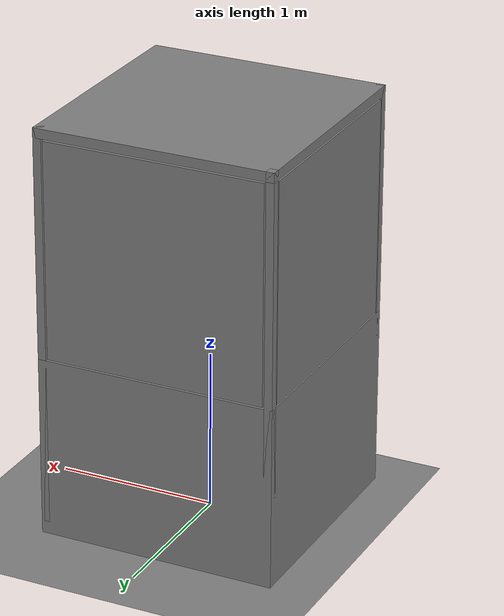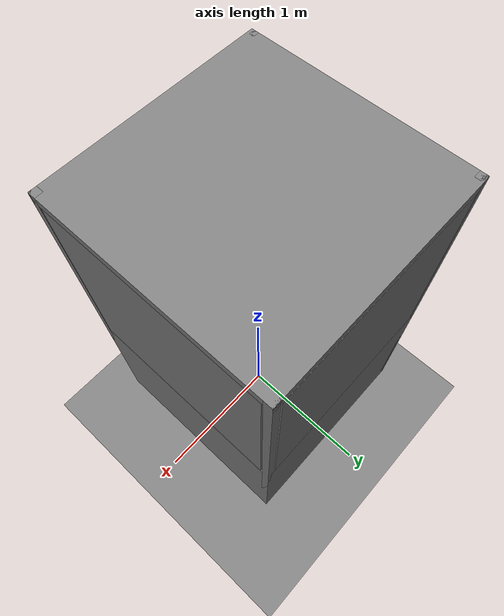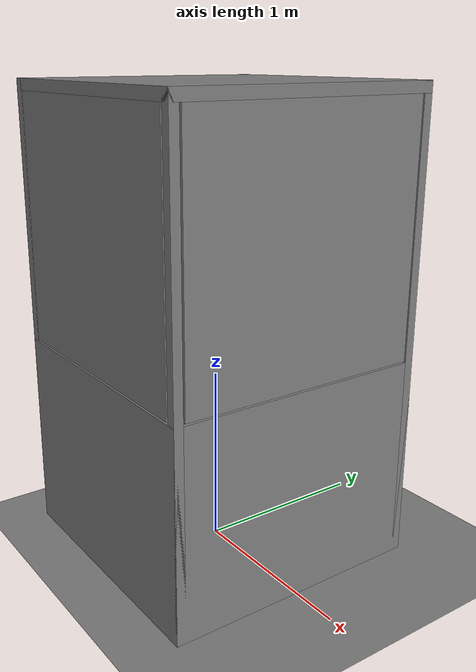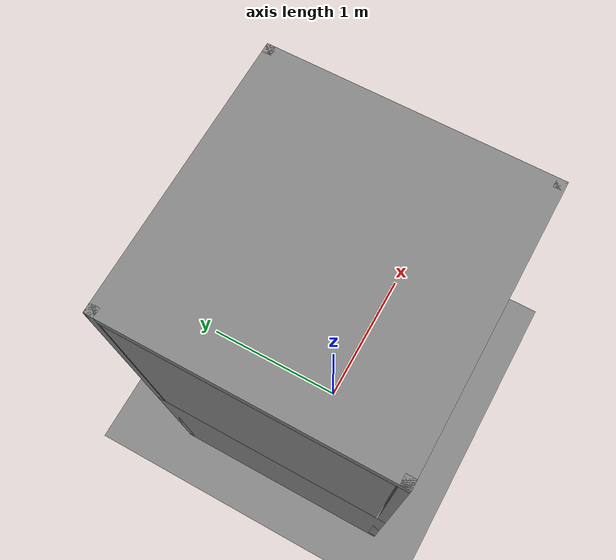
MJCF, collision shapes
<mujoco model="aic_world">
  <compiler angle="radian"/>

  <option gravity="0 0 -9.8" magnetic="5.5645e-06 2.28758e-05 -4.23884e-05"/>

  <visual>
    <headlight ambient="0 0 0" diffuse="0 0 0" specular="0 0 0"/>
  </visual>

  <default>
    <default class="world_default"/>
    <default class="cable_default">
      <joint damping="0.2"/>
    </default>
    <default class="sc_port_default">
      <geom friction="0.5 0.5"/>
    </default>
    <default class="nic_card_default">
      <geom friction="0.1 0.005 0.1"/>
    </default>
  </default>

  <extension>
    <plugin plugin="mujoco.elasticity.cable">
      <instance name="composite">
        <config key="twist" value="1e2"/>
        <config key="bend" value="4e1"/>
      </instance>
    </plugin>
  </extension>

  <asset>
    <texture type="2d" colorspace="linear" name="texture_7d2d03d984e0bd4273d245008f309f6a2ab0c0d6961ab1d51b3160a265d7b5a4_floor_visual_Plane" file="7d2d03d984e0bd4273d245008f309f6a2ab0c0d6961ab1d51b3160a265d7b5a4_floor_visual_b3a94635-54d6beff6424435d3828cb4c8a1278d9ea3964b0.png"/>
    <texture type="2d" colorspace="linear" name="texture_f9b7abd4aff4f6ca20f93c5fe58d59063f878893c8c44b0ffe569a5291eee046_sc_port_visual_FOA-005A_3D_v1.006" file="f9b7abd4aff4f6ca20f93c5fe58d59063f878893c8c44b0ffe569a5291eee046_sc_port_visual_dde5a3d8-80fba2240c77c79deed3a9c104fc19aae11de3a0.png"/>
    <texture type="2d" colorspace="linear" name="texture_eb844ba3a06b0888f9b45b9f67fc3733291f98cdcae567ac4695161ef383009a_nic_card_visual_merged_0" file="eb844ba3a06b0888f9b45b9f67fc3733291f98cdcae567ac4695161ef383009a_nic_card_visual_45ced356-decb3c11fd49e8be2155fa2b1c64d354b4b1809a.png"/>
    <texture type="2d" colorspace="linear" name="texture_eb844ba3a06b0888f9b45b9f67fc3733291f98cdcae567ac4695161ef383009a_nic_card_visual_merged_1" file="eb844ba3a06b0888f9b45b9f67fc3733291f98cdcae567ac4695161ef383009a_nic_card_visual_39dce63a-b1ab28e3f7e42255c5bb13a337e50008ebdbcb02.png"/>
    <texture type="2d" colorspace="linear" name="texture_79d083415a0beb7006489abaa2f7f67624ecb5cc84df7fd21d83dada2e2c75a0_lc_plug_visual_merged_0" file="79d083415a0beb7006489abaa2f7f67624ecb5cc84df7fd21d83dada2e2c75a0_lc_plug_visual_03dabf32-0905e8a8aa368516e682f6ec84258100cdb4efef.png"/>
    <texture type="2d" colorspace="linear" name="texture_07ae86fedcbbab3b5759a8a6e79ba15af5075968dd5eac2cb4666913710c9b1a_sfp_module_visual_Body.005" file="07ae86fedcbbab3b5759a8a6e79ba15af5075968dd5eac2cb4666913710c9b1a_sfp_module_visual_8fc63b58-7471eafc55dcb668ae68adfe70a147b363ba3be9.png"/>
    <texture type="2d" colorspace="linear" name="texture_07ae86fedcbbab3b5759a8a6e79ba15af5075968dd5eac2cb4666913710c9b1a_sfp_module_visual_Body.005_1" file="07ae86fedcbbab3b5759a8a6e79ba15af5075968dd5eac2cb4666913710c9b1a_sfp_module_visual_1f09e86a-a4dc4a72bd6e778067310898a5c179607fd78966.png"/>
    <texture type="2d" colorspace="linear" name="texture_39e0c36083c2ebca1948ca6b7f99419210f3b34232289a37761dbe25cefc0443_sc_plug_visual_merged_0" file="39e0c36083c2ebca1948ca6b7f99419210f3b34232289a37761dbe25cefc0443_sc_plug_visual_5875f865-48f62b2f4840d852c7f39a01e6c183037dc1485b.png"/>
    <material name="material_21630dbca88254236676b9eaa3d656b1a410544dc4182b3953f5492d6064c1ce_enclosure_visual_V1014952.001" class="world_default" shininess="30" rgba="0.290196 0.290196 0.290196 1"/>
    <material name="material_21630dbca88254236676b9eaa3d656b1a410544dc4182b3953f5492d6064c1ce_enclosure_visual_V1014952.001_1" class="world_default" shininess="30" rgba="0.129412 0.129412 0.133333 1"/>
    <material name="material_21630dbca88254236676b9eaa3d656b1a410544dc4182b3953f5492d6064c1ce_light_visual_Plane.001" class="world_default" shininess="30" rgba="0.5 0.5 0.5 1"/>
    <material name="material_7d2d03d984e0bd4273d245008f309f6a2ab0c0d6961ab1d51b3160a265d7b5a4_floor_visual_Plane" class="world_default" texture="texture_7d2d03d984e0bd4273d245008f309f6a2ab0c0d6961ab1d51b3160a265d7b5a4_floor_visual_Plane" shininess="30" rgba="0.5 0.5 0.5 1"/>
    <material name="material_7d2d03d984e0bd4273d245008f309f6a2ab0c0d6961ab1d51b3160a265d7b5a4_walls_visual_Curve.001" class="world_default" shininess="30" rgba="0.0196078 0.0196078 0.0196078 1"/>
    <material name="material_7d2d03d984e0bd4273d245008f309f6a2ab0c0d6961ab1d51b3160a265d7b5a4_walls_visual_merged_1" class="world_default" shininess="30" rgba="0.262745 0.262745 0.262745 1"/>
    <material name="material_7d2d03d984e0bd4273d245008f309f6a2ab0c0d6961ab1d51b3160a265d7b5a4_walls_visual_Plane.003_1" class="world_default" shininess="30" rgba="0.8 0.8 0.8 1"/>
    <material name="material_7d2d03d984e0bd4273d245008f309f6a2ab0c0d6961ab1d51b3160a265d7b5a4_walls_visual_Plane.002" class="world_default" shininess="30" rgba="0.207843 0.207843 0.207843 1"/>
    <material name="material_19f4a95a97b71184a4988be290e52b57fe33862b52d650c82c5d8bc673fc5603_base_visual_ISO_4762_-_M3_x_8.019" class="world_default" shininess="30" rgba="0.0352941 0.0352941 0.0313726 1"/>
    <material name="material_19f4a95a97b71184a4988be290e52b57fe33862b52d650c82c5d8bc673fc5603_base_visual_ISO_4762_-_M3_x_8.019_1" class="world_default" shininess="30" rgba="0.0313726 0.0313726 0.0313726 1"/>
    <material name="material_19f4a95a97b71184a4988be290e52b57fe33862b52d650c82c5d8bc673fc5603_base_visual_ISO_4762_-_M3_x_8.019_2" class="world_default" shininess="30" rgba="0.215686 0 0.215686 1"/>
    <material name="material_ffa8ab95e6b413f8201909c54bab3b167d4710d88967dd6e3d34f13c43447666_sc_mount_visual_ISO_4762_-_M2_x_8.040" class="world_default" shininess="30" rgba="0.0352941 0.0352941 0.0313726 1"/>
    <material name="material_ffa8ab95e6b413f8201909c54bab3b167d4710d88967dd6e3d34f13c43447666_sc_mount_visual_ISO_4762_-_M2_x_8.040_1" class="world_default" shininess="30" rgba="0.0313726 0.0313726 0.0313726 1"/>
    <material name="material_0caf49b143bca9a0c9a13d66d2f75335ec2e74c5bba5cfb7bf0c411aed5bc2cd_sfp_mount_visual_ISO_4762_-_M2_x_8.011" class="world_default" shininess="30" rgba="0.0313726 0.0313726 0.0313726 1"/>
    <material name="material_0caf49b143bca9a0c9a13d66d2f75335ec2e74c5bba5cfb7bf0c411aed5bc2cd_sfp_mount_visual_ISO_4762_-_M2_x_8.011_1" class="world_default" shininess="30" rgba="0.0352941 0.0352941 0.0313726 1"/>
    <material name="material_f9b7abd4aff4f6ca20f93c5fe58d59063f878893c8c44b0ffe569a5291eee046_sc_port_visual_FOA-005A_3D_v1.006" class="world_default" texture="texture_f9b7abd4aff4f6ca20f93c5fe58d59063f878893c8c44b0ffe569a5291eee046_sc_port_visual_FOA-005A_3D_v1.006" shininess="30" rgba="0.5 0.5 0.5 1"/>
    <material name="material_f9b7abd4aff4f6ca20f93c5fe58d59063f878893c8c44b0ffe569a5291eee046_sc_port_visual_merged_1" class="world_default" shininess="30" rgba="0.0352941 0.0352941 0.0313726 1"/>
    <material name="material_f9b7abd4aff4f6ca20f93c5fe58d59063f878893c8c44b0ffe569a5291eee046_sc_port_visual_merged_2" class="world_default" shininess="30" rgba="0.0313726 0.0313726 0.0313726 1"/>
    <material name="material_eb844ba3a06b0888f9b45b9f67fc3733291f98cdcae567ac4695161ef383009a_nic_card_mount_visual_ISO_4762_-_M2_x_8.054" class="world_default" shininess="30" rgba="0.0352941 0.0352941 0.0313726 1"/>
    <material name="material_eb844ba3a06b0888f9b45b9f67fc3733291f98cdcae567ac4695161ef383009a_nic_card_mount_visual_ISO_4762_-_M2_x_8.054_1" class="world_default" shininess="30" rgba="0.0313726 0.0313726 0.0313726 1"/>
    <material name="material_eb844ba3a06b0888f9b45b9f67fc3733291f98cdcae567ac4695161ef383009a_nic_card_visual_merged_0" class="world_default" texture="texture_eb844ba3a06b0888f9b45b9f67fc3733291f98cdcae567ac4695161ef383009a_nic_card_visual_merged_0" shininess="30" rgba="0.5 0.5 0.5 1"/>
    <material name="material_eb844ba3a06b0888f9b45b9f67fc3733291f98cdcae567ac4695161ef383009a_nic_card_visual_merged_1" class="world_default" texture="texture_eb844ba3a06b0888f9b45b9f67fc3733291f98cdcae567ac4695161ef383009a_nic_card_visual_merged_1" shininess="30" rgba="0.5 0.5 0.5 1"/>
    <material name="material_eb844ba3a06b0888f9b45b9f67fc3733291f98cdcae567ac4695161ef383009a_nic_card_visual_Plane.029" class="world_default" shininess="30" rgba="0.0235294 0.0392157 0.0117647 1"/>
    <material name="material_eb844ba3a06b0888f9b45b9f67fc3733291f98cdcae567ac4695161ef383009a_nic_card_visual_Cube.007" class="world_default" shininess="30" rgba="0 0 0 1"/>
    <material name="material_79d083415a0beb7006489abaa2f7f67624ecb5cc84df7fd21d83dada2e2c75a0_lc_plug_visual_merged_0" class="world_default" texture="texture_79d083415a0beb7006489abaa2f7f67624ecb5cc84df7fd21d83dada2e2c75a0_lc_plug_visual_merged_0" shininess="30" rgba="0.5 0.5 0.5 1"/>
    <material name="material_07ae86fedcbbab3b5759a8a6e79ba15af5075968dd5eac2cb4666913710c9b1a_sfp_module_visual_Body.005" class="world_default" texture="texture_07ae86fedcbbab3b5759a8a6e79ba15af5075968dd5eac2cb4666913710c9b1a_sfp_module_visual_Body.005" shininess="30" rgba="0.5 0.5 0.5 1"/>
    <material name="material_07ae86fedcbbab3b5759a8a6e79ba15af5075968dd5eac2cb4666913710c9b1a_sfp_module_visual_Body.005_1" class="world_default" texture="texture_07ae86fedcbbab3b5759a8a6e79ba15af5075968dd5eac2cb4666913710c9b1a_sfp_module_visual_Body.005_1" shininess="30" rgba="0.5 0.5 0.5 1"/>
    <material name="material_39e0c36083c2ebca1948ca6b7f99419210f3b34232289a37761dbe25cefc0443_sc_plug_visual_merged_0" class="world_default" texture="texture_39e0c36083c2ebca1948ca6b7f99419210f3b34232289a37761dbe25cefc0443_sc_plug_visual_merged_0" shininess="30" rgba="0.5 0.5 0.5 1"/>
    <mesh name="21630dbca88254236676b9eaa3d656b1a410544dc4182b3953f5492d6064c1ce_enclosure_visual_V1014952.001" class="world_default" content_type="model/obj" file="21630dbca88254236676b9eaa3d656b1a410544dc4182b3953f5492d6064c1ce_enclosure_visual_V1014952.001-c990efe7b9dfe87aa065fd6eb3960ce051ae2aef.obj" inertia="shell"/>
    <mesh name="21630dbca88254236676b9eaa3d656b1a410544dc4182b3953f5492d6064c1ce_enclosure_visual_V1014952.001_1" class="world_default" content_type="model/obj" file="21630dbca88254236676b9eaa3d656b1a410544dc4182b3953f5492d6064c1ce_enclosure_visual_V1014952.001_1-807e07de06af157c84b994a232617507a7059420.obj" inertia="shell"/>
    <mesh name="21630dbca88254236676b9eaa3d656b1a410544dc4182b3953f5492d6064c1ce_light_visual_Plane.001" class="world_default" content_type="model/obj" file="21630dbca88254236676b9eaa3d656b1a410544dc4182b3953f5492d6064c1ce_light_visual_Plane.001-a8a774a80bc239d73769a498eae528b206eebcb0.obj" inertia="shell"/>
    <mesh name="7d2d03d984e0bd4273d245008f309f6a2ab0c0d6961ab1d51b3160a265d7b5a4_floor_visual_Plane" class="world_default" content_type="model/obj" file="7d2d03d984e0bd4273d245008f309f6a2ab0c0d6961ab1d51b3160a265d7b5a4_floor_visual_Plane-4dc7f6150ad7c239769a0860a01efb2015657aea.obj" inertia="shell"/>
    <mesh name="7d2d03d984e0bd4273d245008f309f6a2ab0c0d6961ab1d51b3160a265d7b5a4_walls_visual_Curve.001" class="world_default" content_type="model/obj" file="7d2d03d984e0bd4273d245008f309f6a2ab0c0d6961ab1d51b3160a265d7b5a4_walls_visual_Curve.001-4d7c79ac2e958832fdb15589262141ca1b80d3a5.obj" inertia="shell"/>
    <mesh name="7d2d03d984e0bd4273d245008f309f6a2ab0c0d6961ab1d51b3160a265d7b5a4_walls_visual_merged_1" class="world_default" content_type="model/obj" file="7d2d03d984e0bd4273d245008f309f6a2ab0c0d6961ab1d51b3160a265d7b5a4_walls_visual_merged_1-359a22140d528747936e80bedf90e1437a177a9f.obj" inertia="shell"/>
    <mesh name="7d2d03d984e0bd4273d245008f309f6a2ab0c0d6961ab1d51b3160a265d7b5a4_walls_visual_Plane.003_1" class="world_default" content_type="model/obj" file="7d2d03d984e0bd4273d245008f309f6a2ab0c0d6961ab1d51b3160a265d7b5a4_walls_visual_Plane.003_1-cd05ed21fa19a2784fb772d7519abf7c31c8b85f.obj" inertia="shell"/>
    <mesh name="7d2d03d984e0bd4273d245008f309f6a2ab0c0d6961ab1d51b3160a265d7b5a4_walls_visual_Plane.002" class="world_default" content_type="model/obj" file="7d2d03d984e0bd4273d245008f309f6a2ab0c0d6961ab1d51b3160a265d7b5a4_walls_visual_Plane.002-ee4f781765eec46c2256d941981732d4b1857f24.obj" inertia="shell"/>
    <mesh name="19f4a95a97b71184a4988be290e52b57fe33862b52d650c82c5d8bc673fc5603_base_visual_ISO_4762_-_M3_x_8.019" class="world_default" content_type="model/obj" file="19f4a95a97b71184a4988be290e52b57fe33862b52d650c82c5d8bc673fc5603_base_visual_ISO_4762_-_M3_x_8.019-f814bb518c42769543ab6246809f3fe4af5c2b64.obj" inertia="shell"/>
    <mesh name="19f4a95a97b71184a4988be290e52b57fe33862b52d650c82c5d8bc673fc5603_base_visual_ISO_4762_-_M3_x_8.019_1" class="world_default" content_type="model/obj" file="19f4a95a97b71184a4988be290e52b57fe33862b52d650c82c5d8bc673fc5603_base_visual_ISO_4762_-_M3_x_8.019_1-0b276ba9910a7642121235b62d2afc47c3995782.obj" inertia="shell"/>
    <mesh name="19f4a95a97b71184a4988be290e52b57fe33862b52d650c82c5d8bc673fc5603_base_visual_ISO_4762_-_M3_x_8.019_2" class="world_default" content_type="model/obj" file="19f4a95a97b71184a4988be290e52b57fe33862b52d650c82c5d8bc673fc5603_base_visual_ISO_4762_-_M3_x_8.019_2-7b96569be9572803417c5650ee83c9c883b44191.obj" inertia="shell"/>
    <mesh name="ffa8ab95e6b413f8201909c54bab3b167d4710d88967dd6e3d34f13c43447666_sc_mount_visual_ISO_4762_-_M2_x_8.040" class="world_default" content_type="model/obj" file="ffa8ab95e6b413f8201909c54bab3b167d4710d88967dd6e3d34f13c43447666_sc_mount_visual_ISO_4762_-_M2_x_8.040-78687100ffd558e8f9e1624af1d7c66e544fb2b1.obj" inertia="shell"/>
    <mesh name="ffa8ab95e6b413f8201909c54bab3b167d4710d88967dd6e3d34f13c43447666_sc_mount_visual_ISO_4762_-_M2_x_8.040_1" class="world_default" content_type="model/obj" file="ffa8ab95e6b413f8201909c54bab3b167d4710d88967dd6e3d34f13c43447666_sc_mount_visual_ISO_4762_-_M2_x_8.040_1-b37e6ae2e05f8677f37dfa75affee0820ec2722c.obj" inertia="shell"/>
    <mesh name="0caf49b143bca9a0c9a13d66d2f75335ec2e74c5bba5cfb7bf0c411aed5bc2cd_sfp_mount_visual_ISO_4762_-_M2_x_8.011" class="world_default" content_type="model/obj" file="0caf49b143bca9a0c9a13d66d2f75335ec2e74c5bba5cfb7bf0c411aed5bc2cd_sfp_mount_visual_ISO_4762_-_M2_x_8.011-e79a298280ce559f60558a5df64e118c814f63e4.obj" inertia="shell"/>
    <mesh name="0caf49b143bca9a0c9a13d66d2f75335ec2e74c5bba5cfb7bf0c411aed5bc2cd_sfp_mount_visual_ISO_4762_-_M2_x_8.011_1" class="world_default" content_type="model/obj" file="0caf49b143bca9a0c9a13d66d2f75335ec2e74c5bba5cfb7bf0c411aed5bc2cd_sfp_mount_visual_ISO_4762_-_M2_x_8.011_1-3a79ef8883f6645921d3fa2c67cf381141e6ea26.obj" inertia="shell"/>
    <mesh name="f9b7abd4aff4f6ca20f93c5fe58d59063f878893c8c44b0ffe569a5291eee046_sc_port_visual_FOA-005A_3D_v1.006" class="world_default" content_type="model/obj" file="f9b7abd4aff4f6ca20f93c5fe58d59063f878893c8c44b0ffe569a5291eee046_sc_port_visual_FOA-005A_3D_v1.006-0690c54f8a7d5fd325c57bdd49f081ad4db184ec.obj" inertia="shell"/>
    <mesh name="f9b7abd4aff4f6ca20f93c5fe58d59063f878893c8c44b0ffe569a5291eee046_sc_port_visual_merged_1" class="world_default" content_type="model/obj" file="f9b7abd4aff4f6ca20f93c5fe58d59063f878893c8c44b0ffe569a5291eee046_sc_port_visual_merged_1-31aef5141da75eeb5a734da46bb7eaf48a169650.obj" inertia="shell"/>
    <mesh name="f9b7abd4aff4f6ca20f93c5fe58d59063f878893c8c44b0ffe569a5291eee046_sc_port_visual_merged_2" class="world_default" content_type="model/obj" file="f9b7abd4aff4f6ca20f93c5fe58d59063f878893c8c44b0ffe569a5291eee046_sc_port_visual_merged_2-a5eaa459350ec83eadeb09501472b99f6092b833.obj" inertia="shell"/>
    <mesh name="eb844ba3a06b0888f9b45b9f67fc3733291f98cdcae567ac4695161ef383009a_nic_card_mount_visual_ISO_4762_-_M2_x_8.054" class="world_default" content_type="model/obj" file="eb844ba3a06b0888f9b45b9f67fc3733291f98cdcae567ac4695161ef383009a_nic_card_mount_visual_ISO_4762_-_M2_x_8.054-865f98896565b646973302f5cc3bb20e1474682a.obj" inertia="shell"/>
    <mesh name="eb844ba3a06b0888f9b45b9f67fc3733291f98cdcae567ac4695161ef383009a_nic_card_mount_visual_ISO_4762_-_M2_x_8.054_1" class="world_default" content_type="model/obj" file="eb844ba3a06b0888f9b45b9f67fc3733291f98cdcae567ac4695161ef383009a_nic_card_mount_visual_ISO_4762_-_M2_x_8.054_1-5adcf23490bd5794ededbd17ac1064f40ca2f1d8.obj" inertia="shell"/>
    <mesh name="eb844ba3a06b0888f9b45b9f67fc3733291f98cdcae567ac4695161ef383009a_nic_card_visual_merged_0" class="world_default" content_type="model/obj" file="eb844ba3a06b0888f9b45b9f67fc3733291f98cdcae567ac4695161ef383009a_nic_card_visual_merged_0-b45f6200bfaa68e87732b114c99af8b477e66413.obj" inertia="shell"/>
    <mesh name="eb844ba3a06b0888f9b45b9f67fc3733291f98cdcae567ac4695161ef383009a_nic_card_visual_merged_1" class="world_default" content_type="model/obj" file="eb844ba3a06b0888f9b45b9f67fc3733291f98cdcae567ac4695161ef383009a_nic_card_visual_merged_1-0e349b7b61b9f4e172feb5320f1e8146f966f938.obj" inertia="shell"/>
    <mesh name="eb844ba3a06b0888f9b45b9f67fc3733291f98cdcae567ac4695161ef383009a_nic_card_visual_Plane.029" class="world_default" content_type="model/obj" file="eb844ba3a06b0888f9b45b9f67fc3733291f98cdcae567ac4695161ef383009a_nic_card_visual_Plane.029-3e628f059a97b4e803370a2b5e0abfcfac063972.obj" inertia="shell"/>
    <mesh name="eb844ba3a06b0888f9b45b9f67fc3733291f98cdcae567ac4695161ef383009a_nic_card_visual_Cube.007" class="world_default" content_type="model/obj" file="eb844ba3a06b0888f9b45b9f67fc3733291f98cdcae567ac4695161ef383009a_nic_card_visual_Cube.007-f8fbe4a2582482ceb99cb3e87bdf6d5a3daf05ec.obj" inertia="shell"/>
    <mesh name="79d083415a0beb7006489abaa2f7f67624ecb5cc84df7fd21d83dada2e2c75a0_lc_plug_visual_merged_0" class="world_default" content_type="model/obj" file="79d083415a0beb7006489abaa2f7f67624ecb5cc84df7fd21d83dada2e2c75a0_lc_plug_visual_merged_0-fdaf59710fc3cc118a7df05add4ff4205edda4ef.obj" inertia="shell"/>
    <mesh name="07ae86fedcbbab3b5759a8a6e79ba15af5075968dd5eac2cb4666913710c9b1a_sfp_module_visual_Body.005" class="world_default" content_type="model/obj" file="07ae86fedcbbab3b5759a8a6e79ba15af5075968dd5eac2cb4666913710c9b1a_sfp_module_visual_Body.005-f93147e1e403de321fb70c06a4b1e00f20feb9fd.obj" inertia="shell"/>
    <mesh name="07ae86fedcbbab3b5759a8a6e79ba15af5075968dd5eac2cb4666913710c9b1a_sfp_module_visual_Body.005_1" class="world_default" content_type="model/obj" file="07ae86fedcbbab3b5759a8a6e79ba15af5075968dd5eac2cb4666913710c9b1a_sfp_module_visual_Body.005_1-4af964a95522e2593eb6381eca4f09ef239782c7.obj" inertia="shell"/>
    <mesh name="39e0c36083c2ebca1948ca6b7f99419210f3b34232289a37761dbe25cefc0443_sc_plug_visual_merged_0" class="world_default" content_type="model/obj" file="39e0c36083c2ebca1948ca6b7f99419210f3b34232289a37761dbe25cefc0443_sc_plug_visual_merged_0-67f94accf247f722dd4954d7448d7956402901f2.obj" inertia="shell"/>
  </asset>

  <worldbody>
    <light name="enclosure_light" class="world_default" pos="0 0 2.5" dir="0 0 -1" intensity="0.4" range="2" attenuation="1 0.01 0.001" cutoff="114.592" exponent="0.993023" diffuse="1 1 1" specular="0.1 0.1 0.1"/>
    <light name="ceiling_01" class="world_default" pos="2 2 6" dir="0 0 -1" intensity="2" range="9" castshadow="false" attenuation="1 0.01 0.001" cutoff="360" diffuse="1 1 1" specular="0.1 0.1 0.1"/>
    <light name="ceiling_02" class="world_default" pos="-2 -2 6" dir="0 0 -1" intensity="2" range="9" castshadow="false" attenuation="1 0.01 0.001" cutoff="360" diffuse="1 1 1" specular="0.1 0.1 0.1"/>
    <body name="enclosure_link">
      <inertial pos="0 0 0" mass="1" diaginertia="1 1 1"/>
      <geom name="v1015026001_collider_box" class="world_default" size="0.75 0.569492 0.75" pos="-0.010998 0.009283 0.569706" quat="-1.22475e-07 1.22474e-07 -0.707107 -0.707107" type="box" group="3"/>
      <geom name="v1015028001_collider_box" class="world_default" size="0.0254 0.0254 1.25" pos="0.713602 0.733883 1.3292" quat="1.73205e-07 0 0 -1" type="box" group="3"/>
      <geom name="v1015013001_collider_box" class="world_default" size="0.0304 0.75 0.75" pos="-0.010998 0.009283 2.5488" quat="0.707107 0 -0.707107 0" type="box" group="3"/>
      <geom name="v1015027_collider_box" class="world_default" size="0.0254 0.0254 1.25" pos="-0.735598 0.733883 1.3292" quat="1.73205e-07 0 0 -1" type="box" group="3"/>
      <geom name="v1015029_collider_box" class="world_default" size="0.0254 0.0254 1.25" pos="-0.735598 -0.715317 1.3292" quat="0 1.73205e-07 -1 -1.73205e-07" type="box" group="3"/>
      <geom name="v1015030_collider_box" class="world_default" size="0.0254 0.0254 1.25" pos="0.713602 -0.715317 1.3292" quat="1.73205e-07 0 0 -1" type="box" group="3"/>
      <geom name="enclosure_visual" class="world_default" type="mesh" contype="0" conaffinity="0" material="material_21630dbca88254236676b9eaa3d656b1a410544dc4182b3953f5492d6064c1ce_enclosure_visual_V1014952.001" mesh="21630dbca88254236676b9eaa3d656b1a410544dc4182b3953f5492d6064c1ce_enclosure_visual_V1014952.001"/>
      <geom name="enclosure_visual_0" class="world_default" type="mesh" contype="0" conaffinity="0" material="material_21630dbca88254236676b9eaa3d656b1a410544dc4182b3953f5492d6064c1ce_enclosure_visual_V1014952.001_1" mesh="21630dbca88254236676b9eaa3d656b1a410544dc4182b3953f5492d6064c1ce_enclosure_visual_V1014952.001_1"/>
      <geom name="light_visual" class="world_default" type="mesh" contype="0" conaffinity="0" material="material_21630dbca88254236676b9eaa3d656b1a410544dc4182b3953f5492d6064c1ce_light_visual_Plane.001" mesh="21630dbca88254236676b9eaa3d656b1a410544dc4182b3953f5492d6064c1ce_light_visual_Plane.001"/>
    </body>
    <body name="enclosure_walls_link">
      <inertial pos="0 0 0" mass="1" diaginertia="1 1 1"/>
      <geom name="v1015062006_collider_box" class="world_default" size="0.0250005 0.6796 0.6892" pos="-0.010998 0.734284 1.8288" quat="0.5 0.5 -0.5 -0.5" type="box" group="3"/>
      <geom name="v1015062005_collider_box" class="world_default" size="0.6892 0.6796 0.025" pos="-0.735998 0.009283 1.8288" quat="0.5 0.5 -0.5 -0.5" type="box" group="3"/>
      <geom name="v1015062007_collider_box" class="world_default" size="0.025 0.6846 0.6892" pos="-0.010998 -0.715717 1.8338" quat="0.5 0.5 -0.5 -0.5" type="box" group="3"/>
      <geom name="v1015062008_collider_box" class="world_default" size="0.6892 0.6846 0.025" pos="0.714002 0.009283 1.8338" quat="0.5 0.5 -0.5 -0.5" type="box" group="3"/>
    </body>
    <body name="floor_link">
      <inertial pos="0 0 0" mass="1" diaginertia="1 1 1"/>
      <geom name="floor_cylinder" class="world_default" size="5 5 1" type="plane" group="3"/>
      <geom name="floor_visual" class="world_default" type="mesh" contype="0" conaffinity="0" material="material_7d2d03d984e0bd4273d245008f309f6a2ab0c0d6961ab1d51b3160a265d7b5a4_floor_visual_Plane" mesh="7d2d03d984e0bd4273d245008f309f6a2ab0c0d6961ab1d51b3160a265d7b5a4_floor_visual_Plane"/>
      <geom name="walls_visual" class="world_default" type="mesh" contype="0" conaffinity="0" material="material_7d2d03d984e0bd4273d245008f309f6a2ab0c0d6961ab1d51b3160a265d7b5a4_walls_visual_Curve.001" mesh="7d2d03d984e0bd4273d245008f309f6a2ab0c0d6961ab1d51b3160a265d7b5a4_walls_visual_Curve.001"/>
      <geom name="walls_visual_0" class="world_default" type="mesh" contype="0" conaffinity="0" material="material_7d2d03d984e0bd4273d245008f309f6a2ab0c0d6961ab1d51b3160a265d7b5a4_walls_visual_merged_1" mesh="7d2d03d984e0bd4273d245008f309f6a2ab0c0d6961ab1d51b3160a265d7b5a4_walls_visual_merged_1"/>
      <geom name="walls_visual_1" class="world_default" type="mesh" contype="0" conaffinity="0" material="material_7d2d03d984e0bd4273d245008f309f6a2ab0c0d6961ab1d51b3160a265d7b5a4_walls_visual_Plane.003_1" mesh="7d2d03d984e0bd4273d245008f309f6a2ab0c0d6961ab1d51b3160a265d7b5a4_walls_visual_Plane.003_1"/>
      <geom name="walls_visual_2" class="world_default" type="mesh" contype="0" conaffinity="0" material="material_7d2d03d984e0bd4273d245008f309f6a2ab0c0d6961ab1d51b3160a265d7b5a4_walls_visual_Plane.002" mesh="7d2d03d984e0bd4273d245008f309f6a2ab0c0d6961ab1d51b3160a265d7b5a4_walls_visual_Plane.002"/>
    </body>
    <body name="task_board_base_link" pos="0.115881 -0.209448 1.14" quat="0.99969 -2.11503e-09 5.15089e-09 0.024898">
      <inertial pos="0.00478302 -0.00410155 0.000603774" quat="0.285459 0.606992 -0.29828 0.679046" mass="5.3" diaginertia="0.107794 0.107046 0.103749"/>
      <geom name="task_board_base_link_fixed_joint_lump__v1015083001_collider_box_left_collision" class="world_default" size="0.15 0.114 0.0045" pos="0 -0.1 0.0075" type="box" group="3"/>
      <geom name="task_board_base_link_fixed_joint_lump__v1015083001_collider_right_collision_1" class="world_default" size="0.15 0.0635 0.0045" pos="0 0.149 0.0075" type="box" group="3"/>
      <geom name="task_board_base_link_fixed_joint_lump__v1015083001_collider_mid_collision_2" class="world_default" size="0.07 0.006 0.0045" pos="-0.075 0.05 0.0075" type="box" group="3"/>
      <geom name="task_board_base_link_fixed_joint_lump__v1015083001_collider_bottom_collision_3" class="world_default" size="0.0825 0.2125 0.0045" pos="0.068 0 0.0075" type="box" group="3"/>
      <geom name="task_board_base_link_fixed_joint_lump__v1015083001_collider_top_collision_4" class="world_default" size="0.0075 0.2125 0.0045" pos="-0.143 0 0.0075" type="box" group="3"/>
      <geom name="task_board_base_link_fixed_joint_lump__v1015079011_collider_box_collision_5" class="world_default" size="0.0088735 0.007 0.0025" pos="0.122534 -0.0974723 0.0145" quat="0.888187 0 0 0.459482" type="box" group="3"/>
      <geom name="task_board_base_link_fixed_joint_lump__v1015079011_collider_box.001_collision_6" class="world_default" size="0.012906 0.0016 0.0068995" pos="0.117446 -0.114006 0.025451" quat="0.820578 -0.175836 0.339894 0.424506" type="box" group="3"/>
      <geom name="task_board_base_link_fixed_joint_lump__v1015079011_collider_box.002_collision_7" class="world_default" size="0.012906 0.00115 0.0068995" pos="0.108264 -0.107506 0.025451" quat="0.820578 -0.175836 0.339894 0.424506" type="box" group="3"/>
      <geom name="task_board_base_link_fixed_joint_lump__v1015079011_collider_box003_collider_box_collision_8" class="world_default" size="0.001 0.007 0.0068995" pos="0.108175 -0.117757 0.03387" quat="0.820578 -0.175836 0.339894 0.424506" type="box" group="3"/>
      <geom name="task_board_base_link_fixed_joint_lump__v1015079011_collider_box003_collider_box.001_collision_9" class="world_default" size="0.000921 0.007 0.0068995" pos="0.117947 -0.103951 0.016956" quat="0.820578 -0.175836 0.339894 0.424506" type="box" group="3"/>
      <geom name="task_board_base_link_fixed_joint_lump__v1015079011_collider_box003_collider_box.002_collision_10" class="world_default" size="0.0124785 0.007 0.0025" pos="0.105492 -0.121547 0.0145" quat="0.888187 0 0 0.459482" type="box" group="3"/>
      <geom name="task_board_base_link_fixed_joint_lump__v1015079011_collider_box003_collider_box.003_collision_11" class="world_default" size="0.012906 0.007 0.0006195" pos="0.110269 -0.114799 0.020656" quat="0.820578 -0.175836 0.339894 0.424506" type="box" group="3"/>
      <geom name="task_board_base_link_fixed_joint_lump__v1015079011_collider_box003_collider_box.004_collision_12" class="world_default" size="0.0011105 0.007 0.0046245" pos="0.120446 -0.100421 0.016624" quat="0.888187 0 0 0.459482" type="box" group="3"/>
      <geom name="task_board_base_link_fixed_joint_lump__v1015079011_collider_box003_collider_box004_collider_box_collision_13" class="world_default" size="0.001045 0.007 0.008711" pos="0.105515 -0.121515 0.020711" quat="0.888187 0 0 0.459482" type="box" group="3"/>
      <geom name="task_board_base_link_fixed_joint_lump__v1015079011_collider_box_collision_14" class="world_default" size="0.0088735 0.007 0.0025" pos="0.136683 0.00458066 0.0125" quat="0.994737 0 0 -0.102466" type="box" group="3"/>
      <geom name="task_board_base_link_fixed_joint_lump__v1015079011_collider_box.001_collision_15" class="world_default" size="0.012906 0.0016 0.0068995" pos="0.119493 0.00264417 0.023451" quat="0.919017 0.0392119 0.380669 -0.0946659" type="box" group="3"/>
      <geom name="task_board_base_link_fixed_joint_lump__v1015079011_collider_box.002_collision_16" class="world_default" size="0.012906 0.00115 0.0068995" pos="0.121787 0.0136579 0.023451" quat="0.919017 0.0392119 0.380669 -0.0946659" type="box" group="3"/>
      <geom name="task_board_base_link_fixed_joint_lump__v1015079011_collider_box003_collider_box_collision_17" class="world_default" size="0.001 0.007 0.0068995" pos="0.112353 0.00964681 0.03187" quat="0.919017 0.0392119 0.380669 -0.0946659" type="box" group="3"/>
      <geom name="task_board_base_link_fixed_joint_lump__v1015079011_collider_box003_collider_box.001_collision_18" class="world_default" size="0.000921 0.007 0.0068995" pos="0.128912 0.00619884 0.014956" quat="0.919017 0.0392119 0.380669 -0.0946659" type="box" group="3"/>
      <geom name="task_board_base_link_fixed_joint_lump__v1015079011_collider_box003_collider_box.002_collision_19" class="world_default" size="0.0124785 0.007 0.0025" pos="0.107806 0.0105935 0.0125" quat="0.994737 0 0 -0.102466" type="box" group="3"/>
      <geom name="task_board_base_link_fixed_joint_lump__v1015079011_collider_box003_collider_box.003_collision_20" class="world_default" size="0.012906 0.007 0.0006195" pos="0.115901 0.00890805 0.018656" quat="0.919017 0.0392119 0.380669 -0.0946659" type="box" group="3"/>
      <geom name="task_board_base_link_fixed_joint_lump__v1015079011_collider_box003_collider_box.004_collision_21" class="world_default" size="0.0011105 0.007 0.0046245" pos="0.133146 0.00531718 0.014624" quat="0.994737 0 0 -0.102466" type="box" group="3"/>
      <geom name="task_board_base_link_fixed_joint_lump__v1015079011_collider_box003_collider_box004_collider_box_collision_22" class="world_default" size="0.001045 0.007 0.008711" pos="0.107845 0.0105856 0.018711" quat="0.994737 0 0 -0.102466" type="box" group="3"/>
      <geom name="task_board_base_link_fixed_joint_lump__iso_4762_m2_x_8072_collider_box_collision_23" class="world_default" size="0.0147285 0.008875 0.0025" pos="0.078836 -0.123821 0.0125" quat="0.92639 0 0 -0.376565" type="box" group="3"/>
      <geom name="task_board_base_link_fixed_joint_lump__iso_4762_m2_x_8072_collider_box_001_collision_24" class="world_default" size="0.0192665 0.008875 0.000864" pos="0.0667246 -0.112026 0.027144" quat="0.855873 -0.144105 -0.354514 -0.3479" type="box" group="3"/>
      <geom name="task_board_base_link_fixed_joint_lump__iso_4762_m2_x_8072_collider_box_002_collision_25" class="world_default" size="0.0137425 0.008875 0.001844" pos="0.0755148 -0.120587 0.022684" quat="0.855873 -0.144105 -0.354514 -0.3479" type="box" group="3"/>
      <geom name="task_board_base_link_fixed_joint_lump__iso_4762_m2_x_8072_collider_box_003_collision_26" class="world_default" size="0.0180555 0.0011525 0.005478" pos="0.075606 -0.109895 0.023979" quat="0.855873 -0.144105 -0.354514 -0.3479" type="box" group="3"/>
      <geom name="task_board_base_link_fixed_joint_lump__iso_4762_m2_x_8072_collider_box_004_collision_27" class="world_default" size="0.0180555 0.0009375 0.005815" pos="0.0645082 -0.120948 0.024217" quat="0.855873 -0.144105 -0.354514 -0.3479" type="box" group="3"/>
      <geom name="task_board_base_link_fixed_joint_lump__iso_4762_m2_x_8072_collider_box_005_collision_28" class="world_default" size="0.002532 0.008875 0.005815" pos="0.0621762 -0.107596 0.013231" quat="0.855873 -0.144105 -0.354514 -0.3479" type="box" group="3"/>
      <geom name="task_board_base_link_fixed_joint_lump__iso_4762_m2_x_8072_collider_box_006_collision_29" class="world_default" size="0.0071855 0.008875 0.0025" pos="0.0580089 -0.103538 0.0125" quat="0.92639 0 0 -0.376565" type="box" group="3"/>
      <geom name="task_board_base_link_fixed_joint_lump__iso_4762_m2_x_8072_collider_box_007_collision_30" class="world_default" size="0.0024465 0.008875 0.0083775" pos="0.0811865 -0.12611 0.021771" quat="0.92639 0 0 -0.376565" type="box" group="3"/>
      <geom name="task_board_base_link_fixed_joint_lump__base_visual_visual" class="world_default" type="mesh" contype="0" conaffinity="0" material="material_19f4a95a97b71184a4988be290e52b57fe33862b52d650c82c5d8bc673fc5603_base_visual_ISO_4762_-_M3_x_8.019" mesh="19f4a95a97b71184a4988be290e52b57fe33862b52d650c82c5d8bc673fc5603_base_visual_ISO_4762_-_M3_x_8.019"/>
      <geom name="task_board_base_link_fixed_joint_lump__base_visual_visual_0" class="world_default" type="mesh" contype="0" conaffinity="0" material="material_19f4a95a97b71184a4988be290e52b57fe33862b52d650c82c5d8bc673fc5603_base_visual_ISO_4762_-_M3_x_8.019_1" mesh="19f4a95a97b71184a4988be290e52b57fe33862b52d650c82c5d8bc673fc5603_base_visual_ISO_4762_-_M3_x_8.019_1"/>
      <geom name="task_board_base_link_fixed_joint_lump__base_visual_visual_1" class="world_default" type="mesh" contype="0" conaffinity="0" material="material_19f4a95a97b71184a4988be290e52b57fe33862b52d650c82c5d8bc673fc5603_base_visual_ISO_4762_-_M3_x_8.019_2" mesh="19f4a95a97b71184a4988be290e52b57fe33862b52d650c82c5d8bc673fc5603_base_visual_ISO_4762_-_M3_x_8.019_2"/>
      <geom name="task_board_base_link_fixed_joint_lump__sc_mount_visual_visual_1" class="world_default" pos="0.1 -0.129306 0.012" quat="0.888187 0 0 0.459482" type="mesh" contype="0" conaffinity="0" material="material_ffa8ab95e6b413f8201909c54bab3b167d4710d88967dd6e3d34f13c43447666_sc_mount_visual_ISO_4762_-_M2_x_8.040" mesh="ffa8ab95e6b413f8201909c54bab3b167d4710d88967dd6e3d34f13c43447666_sc_mount_visual_ISO_4762_-_M2_x_8.040"/>
      <geom name="task_board_base_link_fixed_joint_lump__sc_mount_visual_visual_1_0" class="world_default" pos="0.1 -0.129306 0.012" quat="0.888187 0 0 0.459482" type="mesh" contype="0" conaffinity="0" material="material_ffa8ab95e6b413f8201909c54bab3b167d4710d88967dd6e3d34f13c43447666_sc_mount_visual_ISO_4762_-_M2_x_8.040_1" mesh="ffa8ab95e6b413f8201909c54bab3b167d4710d88967dd6e3d34f13c43447666_sc_mount_visual_ISO_4762_-_M2_x_8.040_1"/>
      <geom name="task_board_base_link_fixed_joint_lump__sc_mount_visual_visual_2" class="world_default" pos="0.0985 0.0125313 0.01" quat="0.994737 0 0 -0.102466" type="mesh" contype="0" conaffinity="0" material="material_ffa8ab95e6b413f8201909c54bab3b167d4710d88967dd6e3d34f13c43447666_sc_mount_visual_ISO_4762_-_M2_x_8.040" mesh="ffa8ab95e6b413f8201909c54bab3b167d4710d88967dd6e3d34f13c43447666_sc_mount_visual_ISO_4762_-_M2_x_8.040"/>
      <geom name="task_board_base_link_fixed_joint_lump__sc_mount_visual_visual_2_0" class="world_default" pos="0.0985 0.0125313 0.01" quat="0.994737 0 0 -0.102466" type="mesh" contype="0" conaffinity="0" material="material_ffa8ab95e6b413f8201909c54bab3b167d4710d88967dd6e3d34f13c43447666_sc_mount_visual_ISO_4762_-_M2_x_8.040_1" mesh="ffa8ab95e6b413f8201909c54bab3b167d4710d88967dd6e3d34f13c43447666_sc_mount_visual_ISO_4762_-_M2_x_8.040_1"/>
      <geom name="task_board_base_link_fixed_joint_lump__sfp_mount_visual_visual_3" class="world_default" pos="0.055 -0.100607 0.01" quat="0.92639 0 0 -0.376565" type="mesh" contype="0" conaffinity="0" material="material_0caf49b143bca9a0c9a13d66d2f75335ec2e74c5bba5cfb7bf0c411aed5bc2cd_sfp_mount_visual_ISO_4762_-_M2_x_8.011" mesh="0caf49b143bca9a0c9a13d66d2f75335ec2e74c5bba5cfb7bf0c411aed5bc2cd_sfp_mount_visual_ISO_4762_-_M2_x_8.011"/>
      <geom name="task_board_base_link_fixed_joint_lump__sfp_mount_visual_visual_3_0" class="world_default" pos="0.055 -0.100607 0.01" quat="0.92639 0 0 -0.376565" type="mesh" contype="0" conaffinity="0" material="material_0caf49b143bca9a0c9a13d66d2f75335ec2e74c5bba5cfb7bf0c411aed5bc2cd_sfp_mount_visual_ISO_4762_-_M2_x_8.011_1" mesh="0caf49b143bca9a0c9a13d66d2f75335ec2e74c5bba5cfb7bf0c411aed5bc2cd_sfp_mount_visual_ISO_4762_-_M2_x_8.011_1"/>
      <body name="sc_port_1::sc_port_link" childclass="sc_port_default" pos="-0.0685368 0.0705 0.0165" quat="0.500398 0.5 0.499602 0.5">
        <inertial pos="0 -0.00100271 0.000137321" quat="-0.00185702 0.707104 -0.00185702 0.707104" mass="0.04" diaginertia="6.5519e-06 5.50329e-06 1.86262e-06"/>
        <geom name="cube_collider_box" class="world_default" size="0.0008435 0.013716 0.00465" pos="0.012047 0 0" type="box" group="3"/>
        <geom name="cube_collider_box.001" class="world_default" size="0.0128905 0.0054 0.000425" pos="0 0 0.004225" type="box" group="3"/>
        <geom name="cube_collider_box_mid" class="world_default" size="0.00515 0.013716 0.0003" pos="0 0 0.00435" type="box" group="3"/>
        <geom name="cube_collider_box_mid02" class="world_default" size="0.0025 0.013716 0.0003" pos="0.01 0 0.00435" type="box" group="3"/>
        <geom name="cube_collider_box_mid03" class="world_default" size="0.0025 0.013716 0.0003" pos="-0.01 0 0.00435" type="box" group="3"/>
        <geom name="cube_collider_box.002" class="world_default" size="0.012825 0.013716 0.0003" pos="0 0 -0.00435" type="box" group="3"/>
        <geom name="cube_collider_box.003" class="world_default" size="0.0008435 0.013716 0.00465" pos="-0.012047 0 0" type="box" group="3"/>
        <geom name="cube_collider_box.004" class="world_default" size="0.002742 0.001524 0.00465" pos="-0.014683 0 0" type="box" group="3"/>
        <geom name="cube_collider_box.005" class="world_default" size="0.002742 0.001524 0.00465" pos="0.014683 0 0" type="box" group="3"/>
        <geom name="cube_collider_box.006" class="world_default" size="0.001496 0.013716 0.00465" type="box" group="3"/>
        <geom name="v1015120013_collider_box" class="world_default" size="0.006 0.005 0.0015" pos="0.0183 -0.003 0" quat="0.5 -0.5 0.5 0.5" type="box" group="3"/>
        <geom name="v1015120012_collider_box" class="world_default" size="0.006 0.005 0.0015" pos="-0.0183 -0.003 0" quat="0.5 -0.5 -0.5 -0.5" type="box" group="3"/>
        <geom name="iso 4762 - m2 x 6013_collider_cylinder" class="world_default" size="0.0019 0.004" pos="0.0153 -0.0005 0" quat="0.693475 0.693475 0.138174 -0.138174" type="cylinder" group="3"/>
        <geom name="iso 4762 - m2 x 6012_collider_cylinder" class="world_default" size="0.0019 0.004" pos="-0.0153 -0.0005 0" quat="0.693475 0.693475 0.138174 -0.138174" type="cylinder" group="3"/>
        <geom name="contact_collision" class="world_default" size="0.0125 0.001473 0.0045" pos="0 -0.0034 0" quat="1.73205e-07 -1 0 0" type="box" group="3"/>
        <geom name="sc_port_visual" class="world_default" type="mesh" contype="0" conaffinity="0" material="material_f9b7abd4aff4f6ca20f93c5fe58d59063f878893c8c44b0ffe569a5291eee046_sc_port_visual_FOA-005A_3D_v1.006" mesh="f9b7abd4aff4f6ca20f93c5fe58d59063f878893c8c44b0ffe569a5291eee046_sc_port_visual_FOA-005A_3D_v1.006"/>
        <geom name="sc_port_visual_0" class="world_default" type="mesh" contype="0" conaffinity="0" material="material_f9b7abd4aff4f6ca20f93c5fe58d59063f878893c8c44b0ffe569a5291eee046_sc_port_visual_merged_1" mesh="f9b7abd4aff4f6ca20f93c5fe58d59063f878893c8c44b0ffe569a5291eee046_sc_port_visual_merged_1"/>
        <geom name="sc_port_visual_1" class="world_default" type="mesh" contype="0" conaffinity="0" material="material_f9b7abd4aff4f6ca20f93c5fe58d59063f878893c8c44b0ffe569a5291eee046_sc_port_visual_merged_2" mesh="f9b7abd4aff4f6ca20f93c5fe58d59063f878893c8c44b0ffe569a5291eee046_sc_port_visual_merged_2"/>
        <site name="sc_port_sensor" class="world_default" pos="0 0 0"/>
        <body name="sc_port_base_link" pos="0 -0.002 0" quat="9.38184e-07 9.38187e-07 0.707105 -0.707108">
          <inertial pos="0 0 0" mass="1" diaginertia="1 1 1"/>
          <body name="sc_port_base_link_entrance" pos="0 0 -0.01564">
            <inertial pos="0 0 0" mass="1" diaginertia="1 1 1"/>
          </body>
        </body>
      </body>
      <body name="nic_card_mount_1::nic_card_mount_link" childclass="nic_card_default" pos="-0.0837212 -0.1345 0.012" quat="0.997909 0 0 0.0646353">
        <inertial pos="0 0 0" mass="1" diaginertia="1 1 1"/>
        <geom name="v1015085006_collider_box" class="world_default" size="0.0025035 0.036998 0.0775" pos="0.006002 -0.025497 0.0875" quat="0.707107 0 0 0.707107" type="box" group="3"/>
        <geom name="v1015085006_collider_box.001" class="world_default" size="0.0125 0.01075 0.007" pos="-0.0555 -0.0155 0.172" quat="0.707107 0 0 0.707107" type="box" group="3"/>
        <geom name="v1015085006_collider_box.002" class="world_default" size="0.01375 0.002532 0.0515" pos="0.038535 -0.01425 0.1155" quat="0.707107 0 0 0.707107" type="box" group="3"/>
        <geom name="v1015085006_collider_box.003" class="world_default" size="0.010003 0.044894 0.0075" pos="-0.001997 -0.017997 0.0075" quat="0.707107 0 0 0.707107" type="box" group="3"/>
        <geom name="v1015085006_collider_box004_collider_box" class="world_default" size="0.0025005 0.02575 0.0075" pos="-0.042132 -0.025499 0.151803" quat="0.653335 0.270468 0.270468 0.653335" type="box" group="3"/>
        <geom name="v1015085006_collider_box.005" class="world_default" size="0.008 0.01 0.0075" pos="-0.043 -0.0198 0.1665" quat="0.65401 0.268834 0.268834 0.654009" type="box" group="3"/>
        <geom name="v1015085011_collider_box" class="world_default" size="0.0078345 0.031 0.0025" pos="3e-06 -0.004871 0.0025" quat="0.707107 0 0 0.707107" type="box" group="3"/>
        <geom name="nic_card_mount_visual" class="world_default" type="mesh" contype="0" conaffinity="0" material="material_eb844ba3a06b0888f9b45b9f67fc3733291f98cdcae567ac4695161ef383009a_nic_card_mount_visual_ISO_4762_-_M2_x_8.054" mesh="eb844ba3a06b0888f9b45b9f67fc3733291f98cdcae567ac4695161ef383009a_nic_card_mount_visual_ISO_4762_-_M2_x_8.054"/>
        <geom name="nic_card_mount_visual_0" class="world_default" type="mesh" contype="0" conaffinity="0" material="material_eb844ba3a06b0888f9b45b9f67fc3733291f98cdcae567ac4695161ef383009a_nic_card_mount_visual_ISO_4762_-_M2_x_8.054_1" mesh="eb844ba3a06b0888f9b45b9f67fc3733291f98cdcae567ac4695161ef383009a_nic_card_mount_visual_ISO_4762_-_M2_x_8.054_1"/>
        <body name="nic_card_link" pos="-0.002 -0.01785 0.0899" quat="0.707388 -0.706825 0 0">
          <inertial pos="0.00150732 -0.00850988 0.00340281" quat="0.506895 0.50066 -0.499024 0.493328" mass="0.15" diaginertia="0.000228137 0.000185186 4.94971e-05"/>
          <geom name="pcb_collider_box" class="world_default" size="0.028 0.0725 0.0008" pos="0 0 -0.0008" type="box" group="3"/>
          <geom name="pcb_collider_box.001" class="world_default" size="0.0345 0.0255 0.0008" pos="0.0065 -0.0025 -0.0008" type="box" group="3"/>
          <geom name="pcb_collider_box.002" class="world_default" size="0.032 0.04775 0.0008" pos="0.004 -0.02475 -0.0008" type="box" group="3"/>
          <geom name="cylinder015_collider_cylinder" class="world_default" size="0.00268 0.002757" pos="0.03175 -0.063 -0.000988" type="cylinder" group="3"/>
          <geom name="cylinder017_collider_cylinder" class="world_default" size="0.00268 0.002759" pos="-0.02225 -0.0675 -0.000986" type="cylinder" group="3"/>
          <geom name="pcb001_collider_box" class="world_default" size="0.005125 0.005125 0.0023015" pos="0.015105 0.054161 0.001899" type="box" group="3"/>
          <geom name="pcb024_collider_box" class="world_default" size="0.0034 0.0034 0.002162" pos="-0.015586 0.055516 0.001759" type="box" group="3"/>
          <geom name="pcb033_collider_box" class="world_default" size="0.021537 0.0208075 0.0011515" pos="-0.002297 0.046302 0.000749" type="box" group="3"/>
          <geom name="cube001_collider_box" class="world_default" size="0.002 0.07 0.00575" pos="0.025006 -0.00041 0.00575" type="box" group="3"/>
          <geom name="cube001_collider_box.001" class="world_default" size="0.0235 0.026 0.0055" pos="-0.0029 -0.0015 0.008" type="box" group="3"/>
          <geom name="10099100-011lfc001_collider_box" class="world_default" size="0.0005495 0.02436 0.0055415" pos="-0.018049 -0.052954 0.00548" quat="0.00675028 0.999977 0 0" type="box" group="3"/>
          <geom name="10099100-011lfc001_collider_box.001" class="world_default" size="0.0005625 0.02436 0.0055605" pos="-0.002437 -0.052954 0.005461" quat="0.00675028 0.999977 0 0" type="box" group="3"/>
          <geom name="10099100-011lfc001_collider_box.002" class="world_default" size="0.008112 0.02436 0.0004615" pos="-0.010237 -0.052889 0.010484" quat="0.00675028 0.999977 0 0" type="box" group="3"/>
          <geom name="10099100-011lfc001_collider_box.003" class="world_default" size="0.008112 0.02436 0.000527" pos="-0.010237 -0.053024 4.6e-05" quat="0.00675028 0.999977 0 0" type="box" group="3"/>
          <geom name="10099100-011lfc001_collider_box.004" class="world_default" size="0.008112 0.000125 0.006849" pos="-0.010237 -0.028738 0.003845" quat="0.00675028 0.999977 0 0" type="box" group="3"/>
          <geom name="10099100-011lfc001_collider_box.005" class="world_default" size="0.0005495 0.02436 0.0055415" pos="0.005151 -0.052954 0.00548" quat="0.00675028 0.999977 0 0" type="box" group="3"/>
          <geom name="10099100-011lfc001_collider_box.006" class="world_default" size="0.0005625 0.02436 0.0055605" pos="0.020763 -0.052954 0.005461" quat="0.00675028 0.999977 0 0" type="box" group="3"/>
          <geom name="10099100-011lfc001_collider_box.007" class="world_default" size="0.008112 0.02436 0.0004615" pos="0.012963 -0.052889 0.010484" quat="0.00675028 0.999977 0 0" type="box" group="3"/>
          <geom name="10099100-011lfc001_collider_box.008" class="world_default" size="0.008112 0.02436 0.000527" pos="0.012963 -0.053024 4.6e-05" quat="0.00675028 0.999977 0 0" type="box" group="3"/>
          <geom name="10099100-011lfc001_collider_box.009" class="world_default" size="0.008112 0.000125 0.006849" pos="0.012963 -0.028738 0.003845" quat="0.00675028 0.999977 0 0" type="box" group="3"/>
          <geom name="plane001_collider_box" class="world_default" size="0.056701 0.0004375 0.0017245" pos="-0.007649 -0.074646 -0.000751" type="box" group="3"/>
          <geom name="plane001_collider_box.001" class="world_default" size="0.056701 0.0004375 0.002505" pos="-0.007649 -0.074646 0.01352" type="box" group="3"/>
          <geom name="plane001_collider_box.002" class="world_default" size="0.0180905 0.0004375 0.0055615" pos="0.038559 -0.074646 0.006455" type="box" group="3"/>
          <geom name="plane001_collider_box.003" class="world_default" size="0.023089 0.0004375 0.0055615" pos="-0.041261 -0.074646 0.006455" type="box" group="3"/>
          <geom name="plane001_collider_box.004" class="world_default" size="0.0004375 0.00635 0.0105" pos="-0.063913 -0.080558 0.005525" type="box" group="3"/>
          <geom name="plane001_collider_box.005" class="world_default" size="0.032 0.007498 0.0012375" pos="0.004 -0.067206 -0.001238" type="box" group="3"/>
          <geom name="cube001_collider_box.002" class="world_default" size="0.0215 0.024 0.0015745" pos="-0.0029 -0.0015 0.001228" type="box" group="3"/>
          <geom name="plane001_collider_box.006" class="world_default" size="0.038092 0.001584 0.0004385" pos="-0.005942 -0.073499 0.015586" type="box" group="3"/>
          <geom name="contact_collision_01" class="world_default" size="0.004056 0.000125 0.00125" pos="0.012963 -0.0305 0.002845" quat="0.00675028 0.999977 0 0" type="box" group="3"/>
          <geom name="contact_collision_02" class="world_default" size="0.004056 0.000125 0.00125" pos="-0.010237 -0.0305 0.002845" quat="0.00675028 0.999977 0 0" type="box" group="3"/>
          <geom name="contact_collision_01_holder" class="world_default" size="0.004056 0.000125 0.001" pos="0.012963 -0.03 0.008" quat="0.00675028 0.999977 0 0" type="box" group="3"/>
          <geom name="contact_collision_02_holder" class="world_default" size="0.004056 0.000125 0.001" pos="-0.010237 -0.03 0.008" quat="0.00675028 0.999977 0 0" type="box" group="3"/>
          <geom name="nic_card_visual" class="world_default" type="mesh" contype="0" conaffinity="0" material="material_eb844ba3a06b0888f9b45b9f67fc3733291f98cdcae567ac4695161ef383009a_nic_card_visual_merged_0" mesh="eb844ba3a06b0888f9b45b9f67fc3733291f98cdcae567ac4695161ef383009a_nic_card_visual_merged_0"/>
          <geom name="nic_card_visual_0" class="world_default" type="mesh" contype="0" conaffinity="0" material="material_eb844ba3a06b0888f9b45b9f67fc3733291f98cdcae567ac4695161ef383009a_nic_card_visual_merged_1" mesh="eb844ba3a06b0888f9b45b9f67fc3733291f98cdcae567ac4695161ef383009a_nic_card_visual_merged_1"/>
          <geom name="nic_card_visual_1" class="world_default" type="mesh" contype="0" conaffinity="0" material="material_eb844ba3a06b0888f9b45b9f67fc3733291f98cdcae567ac4695161ef383009a_nic_card_visual_Plane.029" mesh="eb844ba3a06b0888f9b45b9f67fc3733291f98cdcae567ac4695161ef383009a_nic_card_visual_Plane.029"/>
          <geom name="nic_card_visual_2" class="world_default" type="mesh" contype="0" conaffinity="0" material="material_eb844ba3a06b0888f9b45b9f67fc3733291f98cdcae567ac4695161ef383009a_nic_card_visual_Cube.007" mesh="eb844ba3a06b0888f9b45b9f67fc3733291f98cdcae567ac4695161ef383009a_nic_card_visual_Cube.007"/>
          <site name="sfp_port_sensor" class="world_default" pos="0 0 0"/>
          <body name="sfp_port_0_link" pos="0.01295 -0.031572 0.00501" quat="0.702339 -0.711842 0 0">
            <inertial pos="0 0 0" mass="1" diaginertia="1 1 1"/>
            <body name="sfp_port_0_link_entrance" pos="0 0 -0.0458">
              <inertial pos="0 0 0" mass="1" diaginertia="1 1 1"/>
            </body>
          </body>
          <body name="sfp_port_1_link" pos="-0.01025 -0.031572 0.00501" quat="0.702339 -0.711842 0 0">
            <inertial pos="0 0 0" mass="1" diaginertia="1 1 1"/>
            <body name="sfp_port_1_link_entrance" pos="0 0 -0.0458">
              <inertial pos="0 0 0" mass="1" diaginertia="1 1 1"/>
            </body>
          </body>
        </body>
      </body>
      <body name="nic_card_mount_2::nic_card_mount_link" childclass="nic_card_default" pos="-0.0827072 -0.0945 0.012" quat="0.999018 0 0 -0.0443148">
        <inertial pos="0 0 0" mass="1" diaginertia="1 1 1"/>
        <geom name="v1015085006_collider_box_0" class="world_default" size="0.0025035 0.036998 0.0775" pos="0.006002 -0.025497 0.0875" quat="0.707107 0 0 0.707107" type="box" group="3"/>
        <geom name="v1015085006_collider_box.001_0" class="world_default" size="0.0125 0.01075 0.007" pos="-0.0555 -0.0155 0.172" quat="0.707107 0 0 0.707107" type="box" group="3"/>
        <geom name="v1015085006_collider_box.002_0" class="world_default" size="0.01375 0.002532 0.0515" pos="0.038535 -0.01425 0.1155" quat="0.707107 0 0 0.707107" type="box" group="3"/>
        <geom name="v1015085006_collider_box.003_0" class="world_default" size="0.010003 0.044894 0.0075" pos="-0.001997 -0.017997 0.0075" quat="0.707107 0 0 0.707107" type="box" group="3"/>
        <geom name="v1015085006_collider_box004_collider_box_0" class="world_default" size="0.0025005 0.02575 0.0075" pos="-0.042132 -0.025499 0.151803" quat="0.653335 0.270468 0.270468 0.653335" type="box" group="3"/>
        <geom name="v1015085006_collider_box.005_0" class="world_default" size="0.008 0.01 0.0075" pos="-0.043 -0.0198 0.1665" quat="0.65401 0.268834 0.268834 0.654009" type="box" group="3"/>
        <geom name="v1015085011_collider_box_0" class="world_default" size="0.0078345 0.031 0.0025" pos="3e-06 -0.004871 0.0025" quat="0.707107 0 0 0.707107" type="box" group="3"/>
        <geom name="nic_card_mount_visual_1" class="world_default" type="mesh" contype="0" conaffinity="0" material="material_eb844ba3a06b0888f9b45b9f67fc3733291f98cdcae567ac4695161ef383009a_nic_card_mount_visual_ISO_4762_-_M2_x_8.054" mesh="eb844ba3a06b0888f9b45b9f67fc3733291f98cdcae567ac4695161ef383009a_nic_card_mount_visual_ISO_4762_-_M2_x_8.054"/>
        <geom name="nic_card_mount_visual_2" class="world_default" type="mesh" contype="0" conaffinity="0" material="material_eb844ba3a06b0888f9b45b9f67fc3733291f98cdcae567ac4695161ef383009a_nic_card_mount_visual_ISO_4762_-_M2_x_8.054_1" mesh="eb844ba3a06b0888f9b45b9f67fc3733291f98cdcae567ac4695161ef383009a_nic_card_mount_visual_ISO_4762_-_M2_x_8.054_1"/>
        <body name="nic_card_link_0" pos="-0.002 -0.01785 0.0899" quat="0.707388 -0.706825 0 0">
          <inertial pos="0.00150732 -0.00850988 0.00340281" quat="0.506895 0.50066 -0.499024 0.493328" mass="0.15" diaginertia="0.000228137 0.000185186 4.94971e-05"/>
          <geom name="pcb_collider_box_0" class="world_default" size="0.028 0.0725 0.0008" pos="0 0 -0.0008" type="box" group="3"/>
          <geom name="pcb_collider_box.001_0" class="world_default" size="0.0345 0.0255 0.0008" pos="0.0065 -0.0025 -0.0008" type="box" group="3"/>
          <geom name="pcb_collider_box.002_0" class="world_default" size="0.032 0.04775 0.0008" pos="0.004 -0.02475 -0.0008" type="box" group="3"/>
          <geom name="cylinder015_collider_cylinder_0" class="world_default" size="0.00268 0.002757" pos="0.03175 -0.063 -0.000988" type="cylinder" group="3"/>
          <geom name="cylinder017_collider_cylinder_0" class="world_default" size="0.00268 0.002759" pos="-0.02225 -0.0675 -0.000986" type="cylinder" group="3"/>
          <geom name="pcb001_collider_box_0" class="world_default" size="0.005125 0.005125 0.0023015" pos="0.015105 0.054161 0.001899" type="box" group="3"/>
          <geom name="pcb024_collider_box_0" class="world_default" size="0.0034 0.0034 0.002162" pos="-0.015586 0.055516 0.001759" type="box" group="3"/>
          <geom name="pcb033_collider_box_0" class="world_default" size="0.021537 0.0208075 0.0011515" pos="-0.002297 0.046302 0.000749" type="box" group="3"/>
          <geom name="cube001_collider_box_0" class="world_default" size="0.002 0.07 0.00575" pos="0.025006 -0.00041 0.00575" type="box" group="3"/>
          <geom name="cube001_collider_box.001_0" class="world_default" size="0.0235 0.026 0.0055" pos="-0.0029 -0.0015 0.008" type="box" group="3"/>
          <geom name="10099100-011lfc001_collider_box_0" class="world_default" size="0.0005495 0.02436 0.0055415" pos="-0.018049 -0.052954 0.00548" quat="0.00675028 0.999977 0 0" type="box" group="3"/>
          <geom name="10099100-011lfc001_collider_box.001_0" class="world_default" size="0.0005625 0.02436 0.0055605" pos="-0.002437 -0.052954 0.005461" quat="0.00675028 0.999977 0 0" type="box" group="3"/>
          <geom name="10099100-011lfc001_collider_box.002_0" class="world_default" size="0.008112 0.02436 0.0004615" pos="-0.010237 -0.052889 0.010484" quat="0.00675028 0.999977 0 0" type="box" group="3"/>
          <geom name="10099100-011lfc001_collider_box.003_0" class="world_default" size="0.008112 0.02436 0.000527" pos="-0.010237 -0.053024 4.6e-05" quat="0.00675028 0.999977 0 0" type="box" group="3"/>
          <geom name="10099100-011lfc001_collider_box.004_0" class="world_default" size="0.008112 0.000125 0.006849" pos="-0.010237 -0.028738 0.003845" quat="0.00675028 0.999977 0 0" type="box" group="3"/>
          <geom name="10099100-011lfc001_collider_box.005_0" class="world_default" size="0.0005495 0.02436 0.0055415" pos="0.005151 -0.052954 0.00548" quat="0.00675028 0.999977 0 0" type="box" group="3"/>
          <geom name="10099100-011lfc001_collider_box.006_0" class="world_default" size="0.0005625 0.02436 0.0055605" pos="0.020763 -0.052954 0.005461" quat="0.00675028 0.999977 0 0" type="box" group="3"/>
          <geom name="10099100-011lfc001_collider_box.007_0" class="world_default" size="0.008112 0.02436 0.0004615" pos="0.012963 -0.052889 0.010484" quat="0.00675028 0.999977 0 0" type="box" group="3"/>
          <geom name="10099100-011lfc001_collider_box.008_0" class="world_default" size="0.008112 0.02436 0.000527" pos="0.012963 -0.053024 4.6e-05" quat="0.00675028 0.999977 0 0" type="box" group="3"/>
          <geom name="10099100-011lfc001_collider_box.009_0" class="world_default" size="0.008112 0.000125 0.006849" pos="0.012963 -0.028738 0.003845" quat="0.00675028 0.999977 0 0" type="box" group="3"/>
          <geom name="plane001_collider_box_0" class="world_default" size="0.056701 0.0004375 0.0017245" pos="-0.007649 -0.074646 -0.000751" type="box" group="3"/>
          <geom name="plane001_collider_box.001_0" class="world_default" size="0.056701 0.0004375 0.002505" pos="-0.007649 -0.074646 0.01352" type="box" group="3"/>
          <geom name="plane001_collider_box.002_0" class="world_default" size="0.0180905 0.0004375 0.0055615" pos="0.038559 -0.074646 0.006455" type="box" group="3"/>
          <geom name="plane001_collider_box.003_0" class="world_default" size="0.023089 0.0004375 0.0055615" pos="-0.041261 -0.074646 0.006455" type="box" group="3"/>
          <geom name="plane001_collider_box.004_0" class="world_default" size="0.0004375 0.00635 0.0105" pos="-0.063913 -0.080558 0.005525" type="box" group="3"/>
          <geom name="plane001_collider_box.005_0" class="world_default" size="0.032 0.007498 0.0012375" pos="0.004 -0.067206 -0.001238" type="box" group="3"/>
          <geom name="cube001_collider_box.002_0" class="world_default" size="0.0215 0.024 0.0015745" pos="-0.0029 -0.0015 0.001228" type="box" group="3"/>
          <geom name="plane001_collider_box.006_0" class="world_default" size="0.038092 0.001584 0.0004385" pos="-0.005942 -0.073499 0.015586" type="box" group="3"/>
          <geom name="contact_collision_01_0" class="world_default" size="0.004056 0.000125 0.00125" pos="0.012963 -0.0305 0.002845" quat="0.00675028 0.999977 0 0" type="box" group="3"/>
          <geom name="contact_collision_02_0" class="world_default" size="0.004056 0.000125 0.00125" pos="-0.010237 -0.0305 0.002845" quat="0.00675028 0.999977 0 0" type="box" group="3"/>
          <geom name="contact_collision_01_holder_0" class="world_default" size="0.004056 0.000125 0.001" pos="0.012963 -0.03 0.008" quat="0.00675028 0.999977 0 0" type="box" group="3"/>
          <geom name="contact_collision_02_holder_0" class="world_default" size="0.004056 0.000125 0.001" pos="-0.010237 -0.03 0.008" quat="0.00675028 0.999977 0 0" type="box" group="3"/>
          <geom name="nic_card_visual_3" class="world_default" type="mesh" contype="0" conaffinity="0" material="material_eb844ba3a06b0888f9b45b9f67fc3733291f98cdcae567ac4695161ef383009a_nic_card_visual_merged_0" mesh="eb844ba3a06b0888f9b45b9f67fc3733291f98cdcae567ac4695161ef383009a_nic_card_visual_merged_0"/>
          <geom name="nic_card_visual_4" class="world_default" type="mesh" contype="0" conaffinity="0" material="material_eb844ba3a06b0888f9b45b9f67fc3733291f98cdcae567ac4695161ef383009a_nic_card_visual_merged_1" mesh="eb844ba3a06b0888f9b45b9f67fc3733291f98cdcae567ac4695161ef383009a_nic_card_visual_merged_1"/>
          <geom name="nic_card_visual_5" class="world_default" type="mesh" contype="0" conaffinity="0" material="material_eb844ba3a06b0888f9b45b9f67fc3733291f98cdcae567ac4695161ef383009a_nic_card_visual_Plane.029" mesh="eb844ba3a06b0888f9b45b9f67fc3733291f98cdcae567ac4695161ef383009a_nic_card_visual_Plane.029"/>
          <geom name="nic_card_visual_6" class="world_default" type="mesh" contype="0" conaffinity="0" material="material_eb844ba3a06b0888f9b45b9f67fc3733291f98cdcae567ac4695161ef383009a_nic_card_visual_Cube.007" mesh="eb844ba3a06b0888f9b45b9f67fc3733291f98cdcae567ac4695161ef383009a_nic_card_visual_Cube.007"/>
          <site name="sfp_port_sensor_0" class="world_default" pos="0 0 0"/>
          <body name="sfp_port_0_link_0" pos="0.01295 -0.031572 0.00501" quat="0.702339 -0.711842 0 0">
            <inertial pos="0 0 0" mass="1" diaginertia="1 1 1"/>
            <body name="sfp_port_0_link_entrance_0" pos="0 0 -0.0458">
              <inertial pos="0 0 0" mass="1" diaginertia="1 1 1"/>
            </body>
          </body>
          <body name="sfp_port_1_link_0" pos="-0.01025 -0.031572 0.00501" quat="0.702339 -0.711842 0 0">
            <inertial pos="0 0 0" mass="1" diaginertia="1 1 1"/>
            <body name="sfp_port_1_link_entrance_0" pos="0 0 -0.0458">
              <inertial pos="0 0 0" mass="1" diaginertia="1 1 1"/>
            </body>
          </body>
        </body>
      </body>
      <body name="nic_card_mount_4::nic_card_mount_link" childclass="nic_card_default" pos="-0.0783124 -0.0145 0.012" quat="0.99779 0 0 0.0664423">
        <inertial pos="0 0 0" mass="1" diaginertia="1 1 1"/>
        <geom name="v1015085006_collider_box_1" class="world_default" size="0.0025035 0.036998 0.0775" pos="0.006002 -0.025497 0.0875" quat="0.707107 0 0 0.707107" type="box" group="3"/>
        <geom name="v1015085006_collider_box.001_1" class="world_default" size="0.0125 0.01075 0.007" pos="-0.0555 -0.0155 0.172" quat="0.707107 0 0 0.707107" type="box" group="3"/>
        <geom name="v1015085006_collider_box.002_1" class="world_default" size="0.01375 0.002532 0.0515" pos="0.038535 -0.01425 0.1155" quat="0.707107 0 0 0.707107" type="box" group="3"/>
        <geom name="v1015085006_collider_box.003_1" class="world_default" size="0.010003 0.044894 0.0075" pos="-0.001997 -0.017997 0.0075" quat="0.707107 0 0 0.707107" type="box" group="3"/>
        <geom name="v1015085006_collider_box004_collider_box_1" class="world_default" size="0.0025005 0.02575 0.0075" pos="-0.042132 -0.025499 0.151803" quat="0.653335 0.270468 0.270468 0.653335" type="box" group="3"/>
        <geom name="v1015085006_collider_box.005_1" class="world_default" size="0.008 0.01 0.0075" pos="-0.043 -0.0198 0.1665" quat="0.65401 0.268834 0.268834 0.654009" type="box" group="3"/>
        <geom name="v1015085011_collider_box_1" class="world_default" size="0.0078345 0.031 0.0025" pos="3e-06 -0.004871 0.0025" quat="0.707107 0 0 0.707107" type="box" group="3"/>
        <geom name="nic_card_mount_visual_3" class="world_default" type="mesh" contype="0" conaffinity="0" material="material_eb844ba3a06b0888f9b45b9f67fc3733291f98cdcae567ac4695161ef383009a_nic_card_mount_visual_ISO_4762_-_M2_x_8.054" mesh="eb844ba3a06b0888f9b45b9f67fc3733291f98cdcae567ac4695161ef383009a_nic_card_mount_visual_ISO_4762_-_M2_x_8.054"/>
        <geom name="nic_card_mount_visual_4" class="world_default" type="mesh" contype="0" conaffinity="0" material="material_eb844ba3a06b0888f9b45b9f67fc3733291f98cdcae567ac4695161ef383009a_nic_card_mount_visual_ISO_4762_-_M2_x_8.054_1" mesh="eb844ba3a06b0888f9b45b9f67fc3733291f98cdcae567ac4695161ef383009a_nic_card_mount_visual_ISO_4762_-_M2_x_8.054_1"/>
        <body name="nic_card_link_1" pos="-0.002 -0.01785 0.0899" quat="0.707388 -0.706825 0 0">
          <inertial pos="0.00150732 -0.00850988 0.00340281" quat="0.506895 0.50066 -0.499024 0.493328" mass="0.15" diaginertia="0.000228137 0.000185186 4.94971e-05"/>
          <geom name="pcb_collider_box_1" class="world_default" size="0.028 0.0725 0.0008" pos="0 0 -0.0008" type="box" group="3"/>
          <geom name="pcb_collider_box.001_1" class="world_default" size="0.0345 0.0255 0.0008" pos="0.0065 -0.0025 -0.0008" type="box" group="3"/>
          <geom name="pcb_collider_box.002_1" class="world_default" size="0.032 0.04775 0.0008" pos="0.004 -0.02475 -0.0008" type="box" group="3"/>
          <geom name="cylinder015_collider_cylinder_1" class="world_default" size="0.00268 0.002757" pos="0.03175 -0.063 -0.000988" type="cylinder" group="3"/>
          <geom name="cylinder017_collider_cylinder_1" class="world_default" size="0.00268 0.002759" pos="-0.02225 -0.0675 -0.000986" type="cylinder" group="3"/>
          <geom name="pcb001_collider_box_1" class="world_default" size="0.005125 0.005125 0.0023015" pos="0.015105 0.054161 0.001899" type="box" group="3"/>
          <geom name="pcb024_collider_box_1" class="world_default" size="0.0034 0.0034 0.002162" pos="-0.015586 0.055516 0.001759" type="box" group="3"/>
          <geom name="pcb033_collider_box_1" class="world_default" size="0.021537 0.0208075 0.0011515" pos="-0.002297 0.046302 0.000749" type="box" group="3"/>
          <geom name="cube001_collider_box_1" class="world_default" size="0.002 0.07 0.00575" pos="0.025006 -0.00041 0.00575" type="box" group="3"/>
          <geom name="cube001_collider_box.001_1" class="world_default" size="0.0235 0.026 0.0055" pos="-0.0029 -0.0015 0.008" type="box" group="3"/>
          <geom name="10099100-011lfc001_collider_box_1" class="world_default" size="0.0005495 0.02436 0.0055415" pos="-0.018049 -0.052954 0.00548" quat="0.00675028 0.999977 0 0" type="box" group="3"/>
          <geom name="10099100-011lfc001_collider_box.001_1" class="world_default" size="0.0005625 0.02436 0.0055605" pos="-0.002437 -0.052954 0.005461" quat="0.00675028 0.999977 0 0" type="box" group="3"/>
          <geom name="10099100-011lfc001_collider_box.002_1" class="world_default" size="0.008112 0.02436 0.0004615" pos="-0.010237 -0.052889 0.010484" quat="0.00675028 0.999977 0 0" type="box" group="3"/>
          <geom name="10099100-011lfc001_collider_box.003_1" class="world_default" size="0.008112 0.02436 0.000527" pos="-0.010237 -0.053024 4.6e-05" quat="0.00675028 0.999977 0 0" type="box" group="3"/>
          <geom name="10099100-011lfc001_collider_box.004_1" class="world_default" size="0.008112 0.000125 0.006849" pos="-0.010237 -0.028738 0.003845" quat="0.00675028 0.999977 0 0" type="box" group="3"/>
          <geom name="10099100-011lfc001_collider_box.005_1" class="world_default" size="0.0005495 0.02436 0.0055415" pos="0.005151 -0.052954 0.00548" quat="0.00675028 0.999977 0 0" type="box" group="3"/>
          <geom name="10099100-011lfc001_collider_box.006_1" class="world_default" size="0.0005625 0.02436 0.0055605" pos="0.020763 -0.052954 0.005461" quat="0.00675028 0.999977 0 0" type="box" group="3"/>
          <geom name="10099100-011lfc001_collider_box.007_1" class="world_default" size="0.008112 0.02436 0.0004615" pos="0.012963 -0.052889 0.010484" quat="0.00675028 0.999977 0 0" type="box" group="3"/>
          <geom name="10099100-011lfc001_collider_box.008_1" class="world_default" size="0.008112 0.02436 0.000527" pos="0.012963 -0.053024 4.6e-05" quat="0.00675028 0.999977 0 0" type="box" group="3"/>
          <geom name="10099100-011lfc001_collider_box.009_1" class="world_default" size="0.008112 0.000125 0.006849" pos="0.012963 -0.028738 0.003845" quat="0.00675028 0.999977 0 0" type="box" group="3"/>
          <geom name="plane001_collider_box_1" class="world_default" size="0.056701 0.0004375 0.0017245" pos="-0.007649 -0.074646 -0.000751" type="box" group="3"/>
          <geom name="plane001_collider_box.001_1" class="world_default" size="0.056701 0.0004375 0.002505" pos="-0.007649 -0.074646 0.01352" type="box" group="3"/>
          <geom name="plane001_collider_box.002_1" class="world_default" size="0.0180905 0.0004375 0.0055615" pos="0.038559 -0.074646 0.006455" type="box" group="3"/>
          <geom name="plane001_collider_box.003_1" class="world_default" size="0.023089 0.0004375 0.0055615" pos="-0.041261 -0.074646 0.006455" type="box" group="3"/>
          <geom name="plane001_collider_box.004_1" class="world_default" size="0.0004375 0.00635 0.0105" pos="-0.063913 -0.080558 0.005525" type="box" group="3"/>
          <geom name="plane001_collider_box.005_1" class="world_default" size="0.032 0.007498 0.0012375" pos="0.004 -0.067206 -0.001238" type="box" group="3"/>
          <geom name="cube001_collider_box.002_1" class="world_default" size="0.0215 0.024 0.0015745" pos="-0.0029 -0.0015 0.001228" type="box" group="3"/>
          <geom name="plane001_collider_box.006_1" class="world_default" size="0.038092 0.001584 0.0004385" pos="-0.005942 -0.073499 0.015586" type="box" group="3"/>
          <geom name="contact_collision_01_1" class="world_default" size="0.004056 0.000125 0.00125" pos="0.012963 -0.0305 0.002845" quat="0.00675028 0.999977 0 0" type="box" group="3"/>
          <geom name="contact_collision_02_1" class="world_default" size="0.004056 0.000125 0.00125" pos="-0.010237 -0.0305 0.002845" quat="0.00675028 0.999977 0 0" type="box" group="3"/>
          <geom name="contact_collision_01_holder_1" class="world_default" size="0.004056 0.000125 0.001" pos="0.012963 -0.03 0.008" quat="0.00675028 0.999977 0 0" type="box" group="3"/>
          <geom name="contact_collision_02_holder_1" class="world_default" size="0.004056 0.000125 0.001" pos="-0.010237 -0.03 0.008" quat="0.00675028 0.999977 0 0" type="box" group="3"/>
          <geom name="nic_card_visual_7" class="world_default" type="mesh" contype="0" conaffinity="0" material="material_eb844ba3a06b0888f9b45b9f67fc3733291f98cdcae567ac4695161ef383009a_nic_card_visual_merged_0" mesh="eb844ba3a06b0888f9b45b9f67fc3733291f98cdcae567ac4695161ef383009a_nic_card_visual_merged_0"/>
          <geom name="nic_card_visual_8" class="world_default" type="mesh" contype="0" conaffinity="0" material="material_eb844ba3a06b0888f9b45b9f67fc3733291f98cdcae567ac4695161ef383009a_nic_card_visual_merged_1" mesh="eb844ba3a06b0888f9b45b9f67fc3733291f98cdcae567ac4695161ef383009a_nic_card_visual_merged_1"/>
          <geom name="nic_card_visual_9" class="world_default" type="mesh" contype="0" conaffinity="0" material="material_eb844ba3a06b0888f9b45b9f67fc3733291f98cdcae567ac4695161ef383009a_nic_card_visual_Plane.029" mesh="eb844ba3a06b0888f9b45b9f67fc3733291f98cdcae567ac4695161ef383009a_nic_card_visual_Plane.029"/>
          <geom name="nic_card_visual_10" class="world_default" type="mesh" contype="0" conaffinity="0" material="material_eb844ba3a06b0888f9b45b9f67fc3733291f98cdcae567ac4695161ef383009a_nic_card_visual_Cube.007" mesh="eb844ba3a06b0888f9b45b9f67fc3733291f98cdcae567ac4695161ef383009a_nic_card_visual_Cube.007"/>
          <site name="sfp_port_sensor_1" class="world_default" pos="0 0 0"/>
          <body name="sfp_port_0_link_1" pos="0.01295 -0.031572 0.00501" quat="0.702339 -0.711842 0 0">
            <inertial pos="0 0 0" mass="1" diaginertia="1 1 1"/>
            <body name="sfp_port_0_link_entrance_1" pos="0 0 -0.0458">
              <inertial pos="0 0 0" mass="1" diaginertia="1 1 1"/>
            </body>
          </body>
          <body name="sfp_port_1_link_1" pos="-0.01025 -0.031572 0.00501" quat="0.702339 -0.711842 0 0">
            <inertial pos="0 0 0" mass="1" diaginertia="1 1 1"/>
            <body name="sfp_port_1_link_entrance_1" pos="0 0 -0.0458">
              <inertial pos="0 0 0" mass="1" diaginertia="1 1 1"/>
            </body>
          </body>
        </body>
      </body>
    </body>
    <body name="cable_end_0" childclass="cable_default" pos="0.172124 0.029369 1.507828" quat="0.713143 0.312161 -0.049352 0.625737">
      <freejoint name="cable_end_0_free"/>
      <inertial pos="0 0 0" mass="0.0025" diaginertia="1e-6 1e-6 1e-6"/>
      <geom name="base_vis" class="world_default" size="0.002" contype="0" conaffinity="0"/>
      <plugin instance="composite"/>
      <body name="cable_connection_0" pos="3.92796e-08 9.77679e-08 -2.06386e-07" quat="0.568718 -0.758498 -0.304269 -0.0930676">
        <inertial pos="0 0 0" mass="0.01" diaginertia="1e-6 1e-6 1e-6"/>
        <joint name="joint_connection_end_0" class="world_default" pos="0 0 0" type="ball" damping="0.2"/>
        <geom name="visual_0_0" class="world_default" size="0.001 0.00367636" pos="-0.00367636 0.00425 0" quat="0.673802 0.214463 0.673798 -0.214461" type="cylinder" contype="0" conaffinity="0"/>
        <geom name="visual_1_0" class="world_default" size="0.001 0.00367636" pos="-0.00367636 -0.00425 0" quat="0.673802 -0.214463 0.673798 0.214461" type="cylinder" contype="0" conaffinity="0"/>
        <plugin instance="composite"/>
        <body name="link_1" pos="0.00492984 0.0231371 -0.00404642" quat="0.105294 -0.279255 -0.711559 -0.636093">
          <inertial pos="0 0 0" mass="0.0025" diaginertia="1e-6 1e-6 1e-6"/>
          <joint name="joint_end_0" pos="0 0 -0.024" type="ball"/>
          <geom name="link_1_collision" size="0.002 0.018" pos="0 0 0.006" type="cylinder" group="3"/>
          <geom name="sphere_1_collision" size="0.002" pos="0 0 0.024" group="3"/>
          <geom name="link_1_vis" size="0.002 0.024" type="cylinder" contype="0" conaffinity="0"/>
          <geom name="sphere_1_vis" size="0.002" pos="0 0 0.024" contype="0" conaffinity="0"/>
          <plugin instance="composite"/>
          <body name="link_2" pos="0.00607513 -0.00757543 0.0459482" quat="0.978123 0.158237 0.133092 -0.0228807">
            <inertial pos="0 0 0" mass="0.0025" diaginertia="1e-6 1e-6 1e-6"/>
            <joint name="joint_1" pos="0 0 -0.024" type="ball"/>
            <geom name="link_2_collision" size="0.002 0.024" type="cylinder" group="3"/>
            <geom name="sphere_2_collision" size="0.002" pos="0 0 0.024" group="3"/>
            <geom name="link_2_vis" size="0.002 0.024" type="cylinder" contype="0" conaffinity="0"/>
            <geom name="sphere_2_vis" size="0.002" pos="0 0 0.024" contype="0" conaffinity="0"/>
            <plugin instance="composite"/>
            <body name="link_3" pos="0.000340952 -0.0066758 0.0470506" quat="0.989802 0.140274 0.010359 -0.0225243">
              <inertial pos="0 0 0" mass="0.0025" diaginertia="1e-6 1e-6 1e-6"/>
              <joint name="joint_2" pos="0 0 -0.024" type="ball"/>
              <geom name="link_3_collision" size="0.002 0.024" type="cylinder" group="3"/>
              <geom name="sphere_3_collision" size="0.002" pos="0 0 0.024" group="3"/>
              <geom name="link_3_vis" size="0.002 0.024" type="cylinder" contype="0" conaffinity="0"/>
              <geom name="sphere_3_vis" size="0.002" pos="0 0 0.024" contype="0" conaffinity="0"/>
              <plugin instance="composite"/>
              <body name="link_4" pos="-0.00222853 -0.00468313 0.0474331" quat="0.993751 0.0993077 -0.0441895 -0.0253619">
                <inertial pos="0 0 0" mass="0.0025" diaginertia="1e-6 1e-6 1e-6"/>
                <joint name="joint_3" pos="0 0 -0.024" type="ball"/>
                <geom name="link_4_collision" size="0.002 0.024" type="cylinder" group="3"/>
                <geom name="sphere_4_collision" size="0.002" pos="0 0 0.024" group="3"/>
                <geom name="link_4_vis" size="0.002 0.024" type="cylinder" contype="0" conaffinity="0"/>
                <geom name="sphere_4_vis" size="0.002" pos="0 0 0.024" contype="0" conaffinity="0"/>
                <plugin instance="composite"/>
                <body name="link_5" pos="-0.00369738 -0.00315309 0.0475034" quat="0.993975 0.0691461 -0.0746601 -0.0407168">
                  <inertial pos="0 0 0" mass="0.0025" diaginertia="1e-6 1e-6 1e-6"/>
                  <joint name="joint_4" pos="0 0 -0.024" type="ball"/>
                  <geom name="link_5_collision" size="0.002 0.024" type="cylinder" group="3"/>
                  <geom name="sphere_5_collision" size="0.002" pos="0 0 0.024" group="3"/>
                  <geom name="link_5_vis" size="0.002 0.024" type="cylinder" contype="0" conaffinity="0"/>
                  <geom name="sphere_5_vis" size="0.002" pos="0 0 0.024" contype="0" conaffinity="0"/>
                  <plugin instance="composite"/>
                  <body name="link_6" pos="-0.00400593 -0.00180109 0.0475949" quat="0.993715 0.0429887 -0.0812379 -0.0638979">
                    <inertial pos="0 0 0" mass="0.0025" diaginertia="1e-6 1e-6 1e-6"/>
                    <joint name="joint_5" pos="0 0 -0.024" type="ball"/>
                    <geom name="link_6_collision" size="0.002 0.024" type="cylinder" group="3"/>
                    <geom name="sphere_6_collision" size="0.002" pos="0 0 0.024" group="3"/>
                    <geom name="link_6_vis" size="0.002 0.024" type="cylinder" contype="0" conaffinity="0"/>
                    <geom name="sphere_6_vis" size="0.002" pos="0 0 0.024" contype="0" conaffinity="0"/>
                    <plugin instance="composite"/>
                    <body name="link_7" pos="-0.00351396 -0.000709347 0.0477313" quat="0.993357 0.0211894 -0.0718358 -0.0873641">
                      <inertial pos="0 0 0" mass="0.0025" diaginertia="1e-6 1e-6 1e-6"/>
                      <joint name="joint_6" pos="0 0 -0.024" type="ball"/>
                      <geom name="link_7_collision" size="0.002 0.024" type="cylinder" group="3"/>
                      <geom name="sphere_7_collision" size="0.002" pos="0 0 0.024" group="3"/>
                      <geom name="link_7_vis" size="0.002 0.024" type="cylinder" contype="0" conaffinity="0"/>
                      <geom name="sphere_7_vis" size="0.002" pos="0 0 0.024" contype="0" conaffinity="0"/>
                      <plugin instance="composite"/>
                      <body name="link_8" pos="-0.00241321 0.000200783 0.0478783" quat="0.993428 0.00100481 -0.0505069 -0.102709">
                        <inertial pos="0 0 0" mass="0.0025" diaginertia="1e-6 1e-6 1e-6"/>
                        <joint name="joint_7" pos="0 0 -0.024" type="ball"/>
                        <geom name="link_8_collision" size="0.002 0.024" type="cylinder" group="3"/>
                        <geom name="sphere_8_collision" size="0.002" pos="0 0 0.024" group="3"/>
                        <geom name="link_8_vis" size="0.002 0.024" type="cylinder" contype="0" conaffinity="0"/>
                        <geom name="sphere_8_vis" size="0.002" pos="0 0 0.024" contype="0" conaffinity="0"/>
                        <plugin instance="composite"/>
                        <body name="link_9" pos="-0.00117063 0.00100433 0.0479516" quat="0.99397 -0.0182635 -0.0264608 -0.104837">
                          <inertial pos="0 0 0" mass="0.0025" diaginertia="1e-6 1e-6 1e-6"/>
                          <joint name="joint_8" pos="0 0 -0.024" type="ball"/>
                          <geom name="link_9_collision" size="0.002 0.024" type="cylinder" group="3"/>
                          <geom name="sphere_9_collision" size="0.002" pos="0 0 0.024" group="3"/>
                          <geom name="link_9_vis" size="0.002 0.024" type="cylinder" contype="0" conaffinity="0"/>
                          <geom name="sphere_9_vis" size="0.002" pos="0 0 0.024" contype="0" conaffinity="0"/>
                          <plugin instance="composite"/>
                          <body name="link_10" pos="-0.000281659 0.00176707 0.0479335" quat="0.994696 -0.0360846 -0.00938583 -0.0958644">
                            <inertial pos="0 0 0" mass="0.0025" diaginertia="1e-6 1e-6 1e-6"/>
                            <joint name="joint_9" pos="0 0 -0.024" type="ball"/>
                            <geom name="link_10_collision" size="0.002 0.024" type="cylinder" group="3"/>
                            <geom name="sphere_10_collision" size="0.002" pos="0 0 0.024" group="3"/>
                            <geom name="link_10_vis" size="0.002 0.024" type="cylinder" contype="0" conaffinity="0"/>
                            <geom name="sphere_10_vis" size="0.002" pos="0 0 0.024" contype="0" conaffinity="0"/>
                            <plugin instance="composite"/>
                            <body name="link_11" pos="0.00127469 0.00268465 0.0478165" quat="0.993827 -0.0582522 0.0213183 -0.0919757">
                              <inertial pos="0 0 0" mass="0.0025" diaginertia="1e-6 1e-6 1e-6"/>
                              <joint name="joint_10" pos="0 0 -0.024" type="ball"/>
                              <geom name="link_11_collision" size="0.002 0.024" type="cylinder" group="3"/>
                              <geom name="sphere_11_collision" size="0.002" pos="0 0 0.024" group="3"/>
                              <geom name="link_11_vis" size="0.002 0.024" type="cylinder" contype="0" conaffinity="0"/>
                              <geom name="sphere_11_vis" size="0.002" pos="0 0 0.024" contype="0" conaffinity="0"/>
                              <plugin instance="composite"/>
                              <body name="link_12" pos="0.00326934 0.00422726 0.0473991" quat="0.991325 -0.0931551 0.0622461 -0.0687147">
                                <inertial pos="0 0 0" mass="0.0025" diaginertia="1e-6 1e-6 1e-6"/>
                                <joint name="joint_11" pos="0 0 -0.024" type="ball"/>
                                <geom name="link_12_collision" size="0.002 0.024" type="cylinder" group="3"/>
                                <geom name="sphere_12_collision" size="0.002" pos="0 0 0.024" group="3"/>
                                <geom name="link_12_vis" size="0.002 0.024" type="cylinder" contype="0" conaffinity="0"/>
                                <geom name="sphere_12_vis" size="0.002" pos="0 0 0.024" contype="0" conaffinity="0"/>
                                <plugin instance="composite"/>
                                <body name="link_13" pos="0.00482188 0.00599184 0.0467349" quat="0.985839 -0.130712 0.096322 -0.0419251">
                                  <inertial pos="0 0 0" mass="0.0025" diaginertia="1e-6 1e-6 1e-6"/>
                                  <joint name="joint_12" pos="0 0 -0.024" type="ball"/>
                                  <geom name="link_13_collision" size="0.002 0.024" type="cylinder" group="3"/>
                                  <geom name="sphere_13_collision" size="0.002" pos="0 0 0.024" group="3"/>
                                  <geom name="link_13_vis" size="0.002 0.024" type="cylinder" contype="0" conaffinity="0"/>
                                  <geom name="sphere_13_vis" size="0.002" pos="0 0 0.024" contype="0" conaffinity="0"/>
                                  <plugin instance="composite"/>
                                  <body name="link_14" pos="0.00591505 0.00751608 0.0460126" quat="0.978947 -0.16192 0.123291 -0.0156268">
                                    <inertial pos="0 0 0" mass="0.0025" diaginertia="1e-6 1e-6 1e-6"/>
                                    <joint name="joint_13" pos="0 0 -0.024" type="ball"/>
                                    <geom name="link_14_collision" size="0.002 0.024" type="cylinder" group="3"/>
                                    <geom name="sphere_14_collision" size="0.002" pos="0 0 0.024" group="3"/>
                                    <geom name="link_14_vis" size="0.002 0.024" type="cylinder" contype="0" conaffinity="0"/>
                                    <geom name="sphere_14_vis" size="0.002" pos="0 0 0.024" contype="0" conaffinity="0"/>
                                    <plugin instance="composite"/>
                                    <body name="link_15" pos="0.00664786 0.00819638 0.0455561" quat="0.974173 -0.174104 0.14357 0.00794721">
                                      <inertial pos="0 0 0" mass="0.0025" diaginertia="1e-6 1e-6 1e-6"/>
                                      <joint name="joint_14" pos="0 0 -0.024" type="ball"/>
                                      <geom name="link_15_collision" size="0.002 0.024" type="cylinder" group="3"/>
                                      <geom name="sphere_15_collision" size="0.002" pos="0 0 0.024" group="3"/>
                                      <geom name="link_15_vis" size="0.002 0.024" type="cylinder" contype="0" conaffinity="0"/>
                                      <geom name="sphere_15_vis" size="0.002" pos="0 0 0.024" contype="0" conaffinity="0"/>
                                      <plugin instance="composite"/>
                                      <body name="link_16" pos="0.00692892 0.00768524 0.0456561" quat="0.974899 -0.160074 0.15244 0.0266642">
                                        <inertial pos="0 0 0" mass="0.0025" diaginertia="1e-6 1e-6 1e-6"/>
                                        <joint name="joint_15" pos="0 0 -0.024" type="ball"/>
                                        <geom name="link_16_collision" size="0.002 0.024" type="cylinder" group="3"/>
                                        <geom name="sphere_16_collision" size="0.002" pos="0 0 0.024" group="3"/>
                                        <geom name="link_16_vis" size="0.002 0.024" type="cylinder" contype="0" conaffinity="0"/>
                                        <geom name="sphere_16_vis" size="0.002" pos="0 0 0.024" contype="0" conaffinity="0"/>
                                        <plugin instance="composite"/>
                                        <body name="link_17" pos="0.00681956 0.00605393 0.0462019" quat="0.980306 -0.122687 0.149777 0.0389292">
                                          <inertial pos="0 0 0" mass="0.0025" diaginertia="1e-6 1e-6 1e-6"/>
                                          <joint name="joint_16" pos="0 0 -0.024" type="ball"/>
                                          <geom name="link_17_collision" size="0.002 0.024" type="cylinder" group="3"/>
                                          <geom name="sphere_17_collision" size="0.002" pos="0 0 0.024" group="3"/>
                                          <geom name="link_17_vis" size="0.002 0.024" type="cylinder" contype="0" conaffinity="0"/>
                                          <geom name="sphere_17_vis" size="0.002" pos="0 0 0.024" contype="0" conaffinity="0"/>
                                          <plugin instance="composite"/>
                                          <body name="link_18" pos="0.00641486 0.00357517 0.0468489" quat="0.986992 -0.0693859 0.138448 0.0431852">
                                            <inertial pos="0 0 0" mass="0.0025" diaginertia="1e-6 1e-6 1e-6"/>
                                            <joint name="joint_17" pos="0 0 -0.024" type="ball"/>
                                            <geom name="link_18_collision" size="0.002 0.024" type="cylinder" group="3"/>
                                            <geom name="sphere_18_collision" size="0.002" pos="0 0 0.024" group="3"/>
                                            <geom name="link_18_vis" size="0.002 0.024" type="cylinder" contype="0" conaffinity="0"/>
                                            <geom name="sphere_18_vis" size="0.002" pos="0 0 0.024" contype="0" conaffinity="0"/>
                                            <plugin instance="composite"/>
                                            <body name="link_19" pos="0.00636925 0.00138217 0.0470992" quat="0.989836 -0.0239453 0.134976 0.0378505">
                                              <inertial pos="0 0 0" mass="0.0025" diaginertia="1e-6 1e-6 1e-6"/>
                                              <joint name="joint_18" pos="0 0 -0.024" type="ball"/>
                                              <geom name="link_19_collision" size="0.002 0.024" type="cylinder" group="3"/>
                                              <geom name="sphere_19_collision" size="0.002" pos="0 0 0.024" group="3"/>
                                              <geom name="link_19_vis" size="0.002 0.024" type="cylinder" contype="0" conaffinity="0"/>
                                              <geom name="sphere_19_vis" size="0.002" pos="0 0 0.024" contype="0" conaffinity="0"/>
                                              <plugin instance="composite"/>
                                              <body name="link_20" pos="0.00585533 -0.00106422 0.0472526" quat="0.991777 0.0257772 0.122261 0.0276867">
                                                <inertial pos="0 0 0" mass="0.0025" diaginertia="1e-6 1e-6 1e-6"/>
                                                <joint name="joint_19" pos="0 0 -0.024" type="ball"/>
                                                <geom name="link_20_collision" size="0.002 0.024" type="cylinder" group="3"/>
                                                <geom name="sphere_20_collision" size="0.002" pos="0 0 0.024" group="3"/>
                                                <geom name="link_20_vis" size="0.002 0.024" type="cylinder" contype="0" conaffinity="0"/>
                                                <geom name="sphere_20_vis" size="0.002" pos="0 0 0.024" contype="0" conaffinity="0"/>
                                                <plugin instance="composite"/>
                                                <body name="cable_connection_1" pos="1.02015e-06 -3.93572e-07 0.0240001" quat="0.776013 0.059386 -0.626628 -0.0401768">
                                                  <inertial pos="0 0 0" mass="0.01" diaginertia="1e-6 1e-6 1e-6"/>
                                                  <joint name="joint_connection_end_1" class="world_default" pos="0 0 0" type="ball"/>
                                                  <geom name="collision_0" class="world_default" size="0.001 0.00180278" pos="0.00180278 -0.002 0" quat="0.676768 0.204909 0.676764 -0.204908" type="cylinder" group="3"/>
                                                  <geom name="collision_1" class="world_default" size="0.001 0.00180278" pos="0.00180278 0.002 0" quat="0.676768 -0.204909 0.676764 0.204908" type="cylinder" group="3"/>
                                                  <geom name="visual_0" class="world_default" size="0.001 0.00180278" pos="0.00180278 -0.002 0" quat="0.676768 0.204909 0.676764 -0.204908" type="cylinder" contype="0" conaffinity="0"/>
                                                  <geom name="visual_1" class="world_default" size="0.001 0.00180278" pos="0.00180278 0.002 0" quat="0.676768 -0.204909 0.676764 0.204908" type="cylinder" contype="0" conaffinity="0"/>
                                                  <plugin instance="composite"/>
                                                  <body name="lc_plug_link" pos="0.0410001 5.98897e-08 9.53886e-08" quat="0.707109 -1.73661e-08 -1.35282e-07 -0.707105">
                                                    <inertial pos="0 -0.00428702 8.58528e-05" quat="0.499139 0.500859 -0.500859 0.499139" mass="0.01" diaginertia="1.82581e-06 1.73585e-06 1.30866e-07"/>
                                                    <geom name="cube_collider_box.003_0" class="world_default" size="0.00225 0.00225 0.01" pos="0.003125 0.0097 0" quat="0.5 -0.5 0.5 0.5" type="box" group="3"/>
                                                    <geom name="cube_collider_box.002_0" class="world_default" size="0.00225 0.00225 0.01" pos="-0.003125 0.0097 0" quat="0.5 -0.5 0.5 0.5" type="box" group="3"/>
                                                    <geom name="cube001_collider_box.003" class="world_default" size="0.0061765 0.0028 0.001625" pos="0 0.002503 0.001434" quat="-1.73205e-07 0 1 0" type="box" group="3"/>
                                                    <geom name="cube001_collider_box.002_2" class="world_default" size="0.003325 0.0028 0.003016" pos="0 0.002503 -0.000413" quat="-1.73205e-07 0 1 0" type="box" group="3"/>
                                                    <geom name="cylinder001_collider_cylinder.001" class="world_default" size="0.000625 0.001502" pos="0.003125 0.0197 0" quat="0.707107 0.707107 0 0" type="cylinder" group="3"/>
                                                    <geom name="cylinder_collider_cylinder.001" class="world_default" size="0.000625 0.001502" pos="-0.003125 0.0197 0" quat="0.707107 0.707107 0 0" type="cylinder" group="3"/>
                                                    <geom name="1af02-003-ma2_collider_cylinder" class="world_default" size="0.002794 0.014351" pos="0.003125 -0.014628 0" quat="0.707107 -0.707107 0 0" type="cylinder" group="3"/>
                                                    <geom name="1af02-003-ma2001_collider_cylinder" class="world_default" size="0.002794 0.014351" pos="-0.003125 -0.014628 0" quat="0.707107 -0.707107 0 0" type="cylinder" group="3"/>
                                                    <geom name="lc_plug_visual" class="world_default" type="mesh" contype="0" conaffinity="0" material="material_79d083415a0beb7006489abaa2f7f67624ecb5cc84df7fd21d83dada2e2c75a0_lc_plug_visual_merged_0" mesh="79d083415a0beb7006489abaa2f7f67624ecb5cc84df7fd21d83dada2e2c75a0_lc_plug_visual_merged_0"/>
                                                    <body name="sfp_module_link" pos="1.24441e-07 0.0384001 8.30288e-08" quat="4.02624e-08 1 1.46612e-06 1.28656e-06">
                                                      <inertial pos="0.000140388 0.0140944 0.000755794" quat="0.500874 0.506 -0.492487 0.500546" mass="0.02" diaginertia="3.76251e-06 3.53019e-06 5.94798e-07"/>
                                                      <geom name="port_collider_box" class="world_default" size="0.00071 0.000375 0.0101875" pos="-0.00571 0.022559 -0.00275" quat="0.707107 0.707107 0 0" type="box" group="3"/>
                                                      <geom name="port_collider_box.001" class="world_default" size="0.00125 0.000375 0.0101875" pos="0 0.022559 -0.00275" quat="0.707107 0.707107 0 0" type="box" group="3"/>
                                                      <geom name="port_collider_box.002" class="world_default" size="0.00642 9.5e-05 0.003651" pos="0 0.02732 -0.00447" quat="0.707107 0.707107 0 0" type="box" group="3"/>
                                                      <geom name="port_collider_box.003" class="world_default" size="0.00046 0.0041395 0.0101875" pos="0.00596 0.022559 -8.7e-05" quat="0.707107 0.707107 0 0" type="box" group="3"/>
                                                      <geom name="port_collider_box.004" class="world_default" size="0.00642 0.000674 0.0101875" pos="0 0.022559 0.003049" quat="0.707107 0.707107 0 0" type="box" group="3"/>
                                                      <geom name="port_collider_box.005" class="world_default" size="0.00046 0.0041395 0.0101875" pos="-0.00596 0.022559 -8.7e-05" quat="0.707107 0.707107 0 0" type="box" group="3"/>
                                                      <geom name="port_collider_box.006" class="world_default" size="0.00071 0.000375 0.0101875" pos="0.00571 0.022559 -0.00275" quat="0.707107 0.707107 0 0" type="box" group="3"/>
                                                      <geom name="port_collider_box.007" class="world_default" size="0.00075 0.0038735 0.0101875" pos="0 0.022559 -0.000239" quat="0.707107 0.707107 0 0" type="box" group="3"/>
                                                      <geom name="port_collider_box.008" class="world_default" size="0.00071 0.000503 0.0064415" pos="-0.00571 0.018813 -0.003546" quat="0.707107 0.707107 0 0" type="box" group="3"/>
                                                      <geom name="port_collider_box.009" class="world_default" size="0.00071 0.000503 0.0064415" pos="0.00571 0.018813 -0.003546" quat="0.707107 0.707107 0 0" type="box" group="3"/>
                                                      <geom name="latch_collider_box" class="world_default" size="0.00692 0.0008005 0.001713" pos="0 0.029531 -0.005175" quat="0.707107 0.707107 0 0" type="box" group="3"/>
                                                      <geom name="latch_collider_box.001" class="world_default" size="0.0005145 0.004772 0.00185" pos="0.006405 0.030896 0.000207" quat="0.707107 0.707107 0 0" type="box" group="3"/>
                                                      <geom name="latch_collider_box.002" class="world_default" size="0.00692 0.0011915 0.00185" pos="0 0.030896 0.004716" quat="0.707107 0.707107 0 0" type="box" group="3"/>
                                                      <geom name="latch_collider_box.003" class="world_default" size="0.0004825 0.004772 0.00185" pos="-0.006437 0.030896 0.000207" quat="0.707107 0.707107 0 0" type="box" group="3"/>
                                                      <geom name="head_collider_box" class="world_default" size="0.000642 0.005125 0.0027" pos="0.006358 0.026353 0.000375" quat="0.707107 0.707107 0 0" type="box" group="3"/>
                                                      <geom name="head_collider_box.001" class="world_default" size="0.000642 0.005485 0.0027" pos="-0.006358 0.026353 0.000765" quat="0.707107 0.707107 0 0" type="box" group="3"/>
                                                      <geom name="head_collider_box.002" class="world_default" size="0.007 0.0011225 0.0027" pos="0 0.026353 0.005128" quat="0.707107 0.707107 0 0" type="box" group="3"/>
                                                      <geom name="head_collider_box.003" class="world_default" size="0.007 0.0001875 0.0027" pos="0 0.026353 -0.004563" quat="0.707107 0.707107 0 0" type="box" group="3"/>
                                                      <geom name="body_collider_box" class="world_default" size="0.006875 0.02365 0.0003945" pos="0 0.001 0.00383" type="box" group="3"/>
                                                      <geom name="body_collider_box.001" class="world_default" size="0.006875 0.02365 8.9e-05" pos="0 0.001 -0.004138" type="box" group="3"/>
                                                      <geom name="body_collider_box.002" class="world_default" size="0.000287 0.02365 0.004225" pos="-0.006588 0.001 0" type="box" group="3"/>
                                                      <geom name="body_collider_box.003" class="world_default" size="0.0004055 0.02365 0.004225" pos="0.00647 0.001 0" type="box" group="3"/>
                                                      <geom name="port_collider_box.010" class="world_default" size="0.00642 0.0038815 0.0058645" pos="0 0.01229 0.000119" quat="0.707107 0.707107 0 0" type="box" group="3"/>
                                                      <geom name="port_collider_box002_collider_box" class="world_default" size="0.00642 0.0002045 0.0008005" pos="0 0.024453 -0.004254" quat="0.707107 0.707107 0 0" type="box" group="3"/>
                                                      <geom name="port_collider_box.011" class="world_default" size="0.00125 0.000503 0.0064415" pos="0 0.018813 -0.003546" quat="0.707107 0.707107 0 0" type="box" group="3"/>
                                                      <geom name="sfp_module_visual" class="world_default" type="mesh" contype="0" conaffinity="0" material="material_07ae86fedcbbab3b5759a8a6e79ba15af5075968dd5eac2cb4666913710c9b1a_sfp_module_visual_Body.005" mesh="07ae86fedcbbab3b5759a8a6e79ba15af5075968dd5eac2cb4666913710c9b1a_sfp_module_visual_Body.005"/>
                                                      <geom name="sfp_module_visual_0" class="world_default" type="mesh" contype="0" conaffinity="0" material="material_07ae86fedcbbab3b5759a8a6e79ba15af5075968dd5eac2cb4666913710c9b1a_sfp_module_visual_Body.005_1" mesh="07ae86fedcbbab3b5759a8a6e79ba15af5075968dd5eac2cb4666913710c9b1a_sfp_module_visual_Body.005_1"/>
                                                      <body name="sfp_tip_link" pos="-2.58585e-07 -0.02365 3.15299e-07" quat="0.707105 0.707108 -1.31899e-07 -5.00978e-07">
                                                        <inertial pos="0 0 0" mass="0.001" diaginertia="1e-06 1e-06 1e-06"/>
                                                        <geom name="contact_collision_0" class="world_default" size="0.006875 0.0021125 0.0005" pos="0 0.0021125 -0.0005" type="box" group="3"/>
                                                        <geom name="non_contact_collision" class="world_default" size="0.006875 0.0021125 0.0005" pos="0 -0.0021125 -0.0005" type="box" group="3"/>
                                                      </body>
                                                    </body>
                                                  </body>
                                                </body>
                                              </body>
                                            </body>
                                          </body>
                                        </body>
                                      </body>
                                    </body>
                                  </body>
                                </body>
                              </body>
                            </body>
                          </body>
                        </body>
                      </body>
                    </body>
                  </body>
                </body>
              </body>
            </body>
          </body>
        </body>
        <body name="sc_plug_link" pos="-0.052 2.01319e-08 1.21977e-08" quat="1.36598e-06 1.23749e-07 -5.0181e-08 1">
          <inertial pos="-0.00907511 4.9566e-05 8.71699e-06" quat="0.000872542 0.70691 -0.000868656 0.707302" mass="0.04" diaginertia="8.85404e-06 7.17322e-06 2.12253e-06"/>
          <geom name="housing blue_predeterminado005_collider_box" class="world_default" size="0.0063605 0.0045 0.00365" pos="0.002038 0.006344 4e-06" type="box" group="3"/>
          <geom name="housing blue_predeterminado005_collider_box.001" class="world_default" size="0.0063605 0.0045 0.00365" pos="0.002038 -0.006344 4e-06" type="box" group="3"/>
          <geom name="housing blue_predeterminado005_collider_box.002" class="world_default" size="0.006861 0.0035 0.00365" pos="0.002539 0.006344 4e-06" type="box" group="3"/>
          <geom name="housing blue_predeterminado005_collider_box.003" class="world_default" size="0.006861 0.0035 0.00365" pos="0.002539 -0.006344 4e-06" type="box" group="3"/>
          <geom name="housing blue_predeterminado005_collider_box.004" class="world_default" size="0.001 0.000705 0.00365" pos="0.008191 0.003056 4e-06" quat="0.92388 0 0 -0.382683" type="box" group="3"/>
          <geom name="housing blue_predeterminado005_collider_box.005" class="world_default" size="0.001 0.000705 0.00365" pos="0.008191 0.009636 4e-06" quat="0.92388 0 0 0.382683" type="box" group="3"/>
          <geom name="housing blue_predeterminado005_collider_box.006" class="world_default" size="0.001 0.000705 0.00365" pos="0.008191 -0.009636 4e-06" quat="0.92388 0 0 -0.382683" type="box" group="3"/>
          <geom name="housing blue_predeterminado005_collider_box.007" class="world_default" size="0.001 0.000705 0.00365" pos="0.008191 -0.003056 4e-06" quat="0.92388 0 0 0.382683" type="box" group="3"/>
          <geom name="cube002_collider_box" class="world_default" size="0.006275 0.0125 0.00505" pos="-0.010291 0 0" type="box" group="3"/>
          <geom name="cylinder011_collider_cylinder" class="world_default" size="0.0029 0.014605" pos="-0.031147 -0.00635 0" quat="0.707107 0 0.707107 0" type="cylinder" group="3"/>
          <geom name="cylinder005_collider_cylinder" class="world_default" size="0.0029 0.015799" pos="-0.029953 0.00635 0" quat="0.707107 0 0.707107 0" type="cylinder" group="3"/>
          <geom name="ferula_predeterminado005_collider_cylinder" class="world_default" size="0.00125 0.007" pos="0.00465 -0.00635 0" quat="0.707107 0 0.707107 0" type="cylinder" group="3"/>
          <geom name="ferula_predeterminado003_collider_cylinder" class="world_default" size="0.00125 0.007" pos="0.00465 0.00635 0" quat="0.707107 0 0.707107 0" type="cylinder" group="3"/>
          <geom name="side_box_collision" class="world_default" size="0.002125 0.00081 0.0005" pos="0.00146 -0.00632 0.0042" type="box" group="3"/>
          <geom name="side_box_collision_2" class="world_default" size="0.002125 0.00081 0.0005" pos="0.00146 0.00632 0.0042" type="box" group="3"/>
          <geom name="sc_plug_visual" class="world_default" type="mesh" contype="0" conaffinity="0" material="material_39e0c36083c2ebca1948ca6b7f99419210f3b34232289a37761dbe25cefc0443_sc_plug_visual_merged_0" mesh="39e0c36083c2ebca1948ca6b7f99419210f3b34232289a37761dbe25cefc0443_sc_plug_visual_merged_0"/>
          <body name="sc_tip_link" pos="0.0116499 3.96054e-08 -2.02387e-09" quat="0.499998 -0.5 0.500002 -0.5">
            <inertial pos="0 0 0" mass="0.001" diaginertia="1e-06 1e-06 1e-06"/>
          </body>
        </body>
      </body>
    </body>
    <body name="static_link">
      <inertial pos="0 0 0" mass="1" diaginertia="1 1 1"/>
    </body>
    <body name="static_link_0">
      <inertial pos="0 0 0" mass="1" diaginertia="1 1 1"/>
    </body>
  </worldbody>

  <contact>
    <exclude name="task_board_base_link_sc_port_1::sc_port_link" body1="task_board_base_link" body2="sc_port_1::sc_port_link"/>
    <exclude name="task_board_base_link_nic_card_mount_1::nic_card_mount_link" body1="task_board_base_link" body2="nic_card_mount_1::nic_card_mount_link"/>
    <exclude name="task_board_base_link_nic_card_mount_2::nic_card_mount_link" body1="task_board_base_link" body2="nic_card_mount_2::nic_card_mount_link"/>
    <exclude name="task_board_base_link_nic_card_mount_4::nic_card_mount_link" body1="task_board_base_link" body2="nic_card_mount_4::nic_card_mount_link"/>
    <exclude body1="sc_port_1::sc_port_link" body2="sc_plug_link"/>
    <exclude body1="cable_end_0" body2="link_1"/>
  </contact>

  <equality>
    <weld body1="ati/tool_link" body2="sc_plug_link" relpose="-0.000980 0.000693 0.180020 0.170140 -0.684594 0.157796 -0.691002" solref="0.002 1" solimp="0.99 0.999 0.001"/>
  </equality>
</mujoco>
